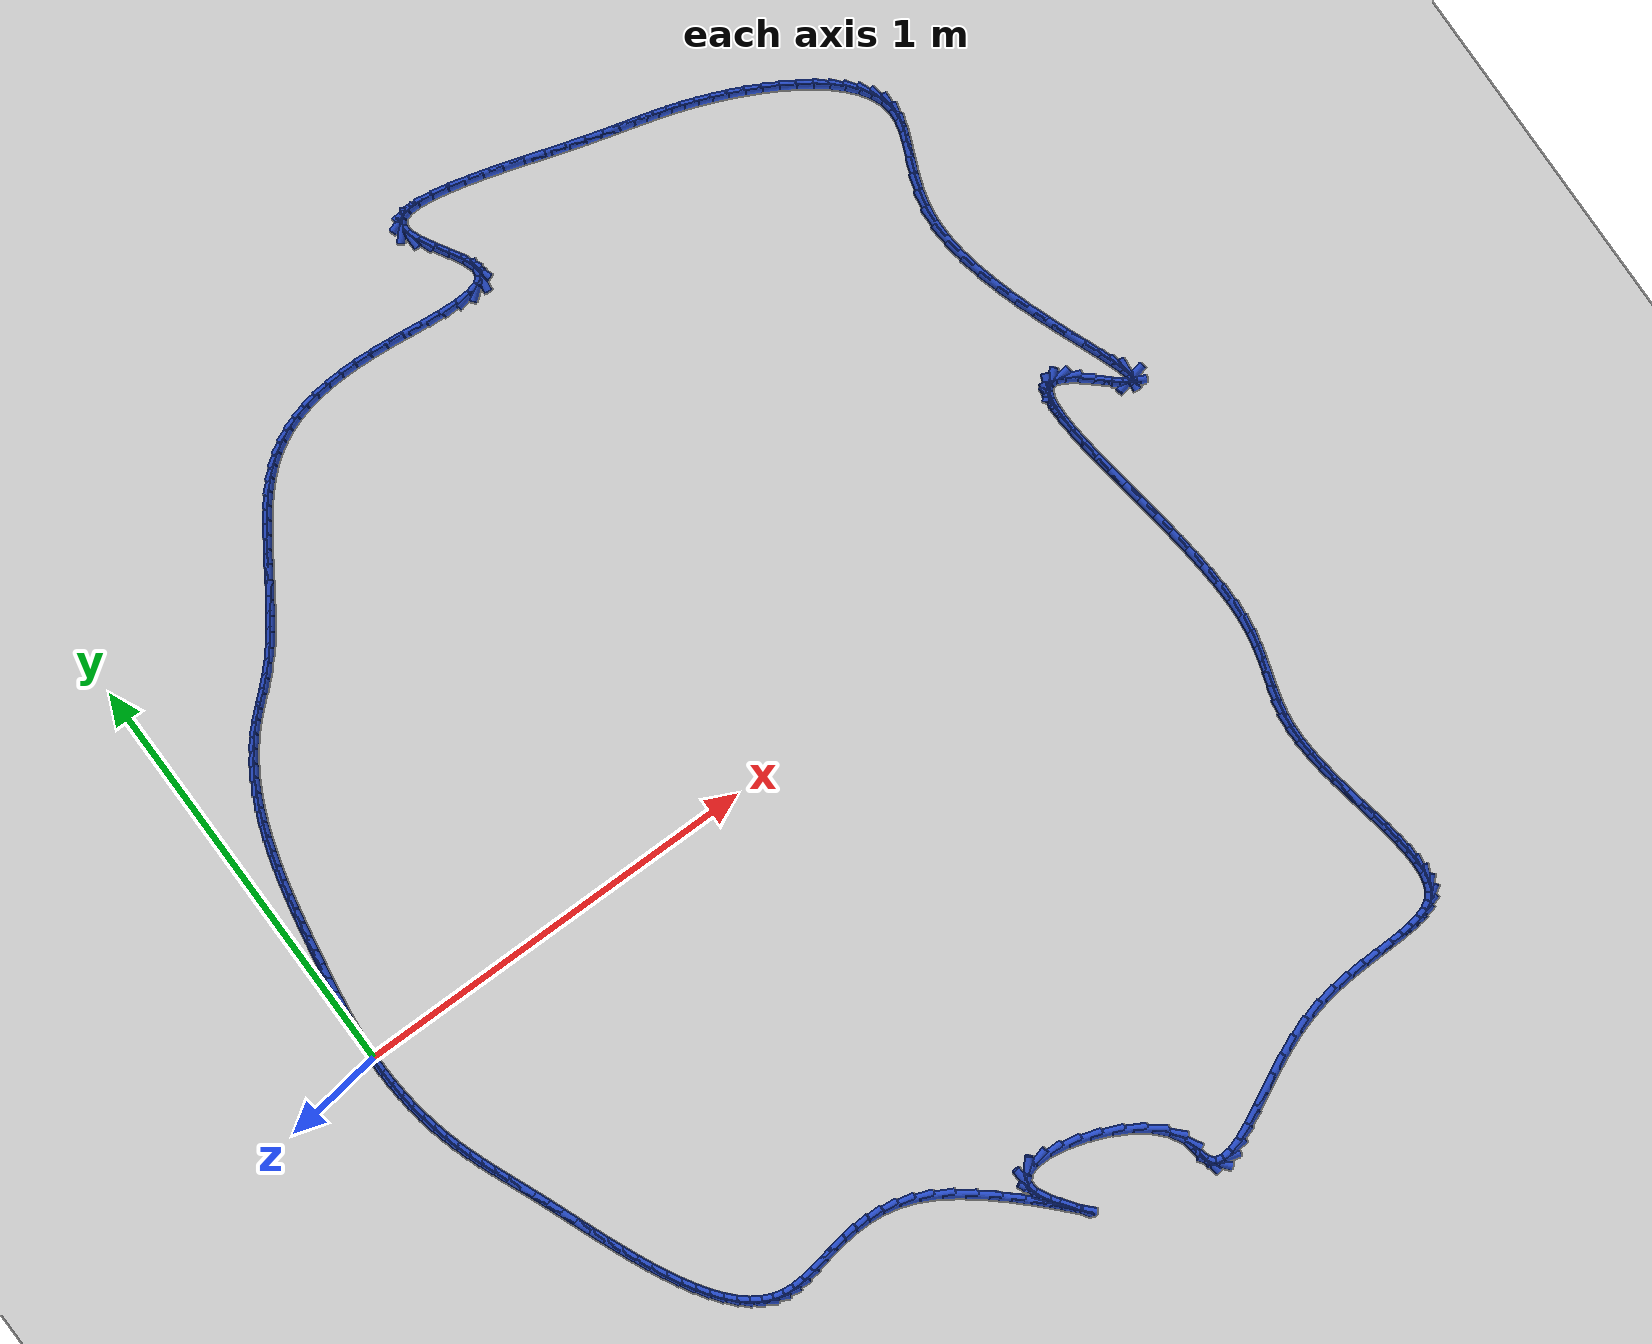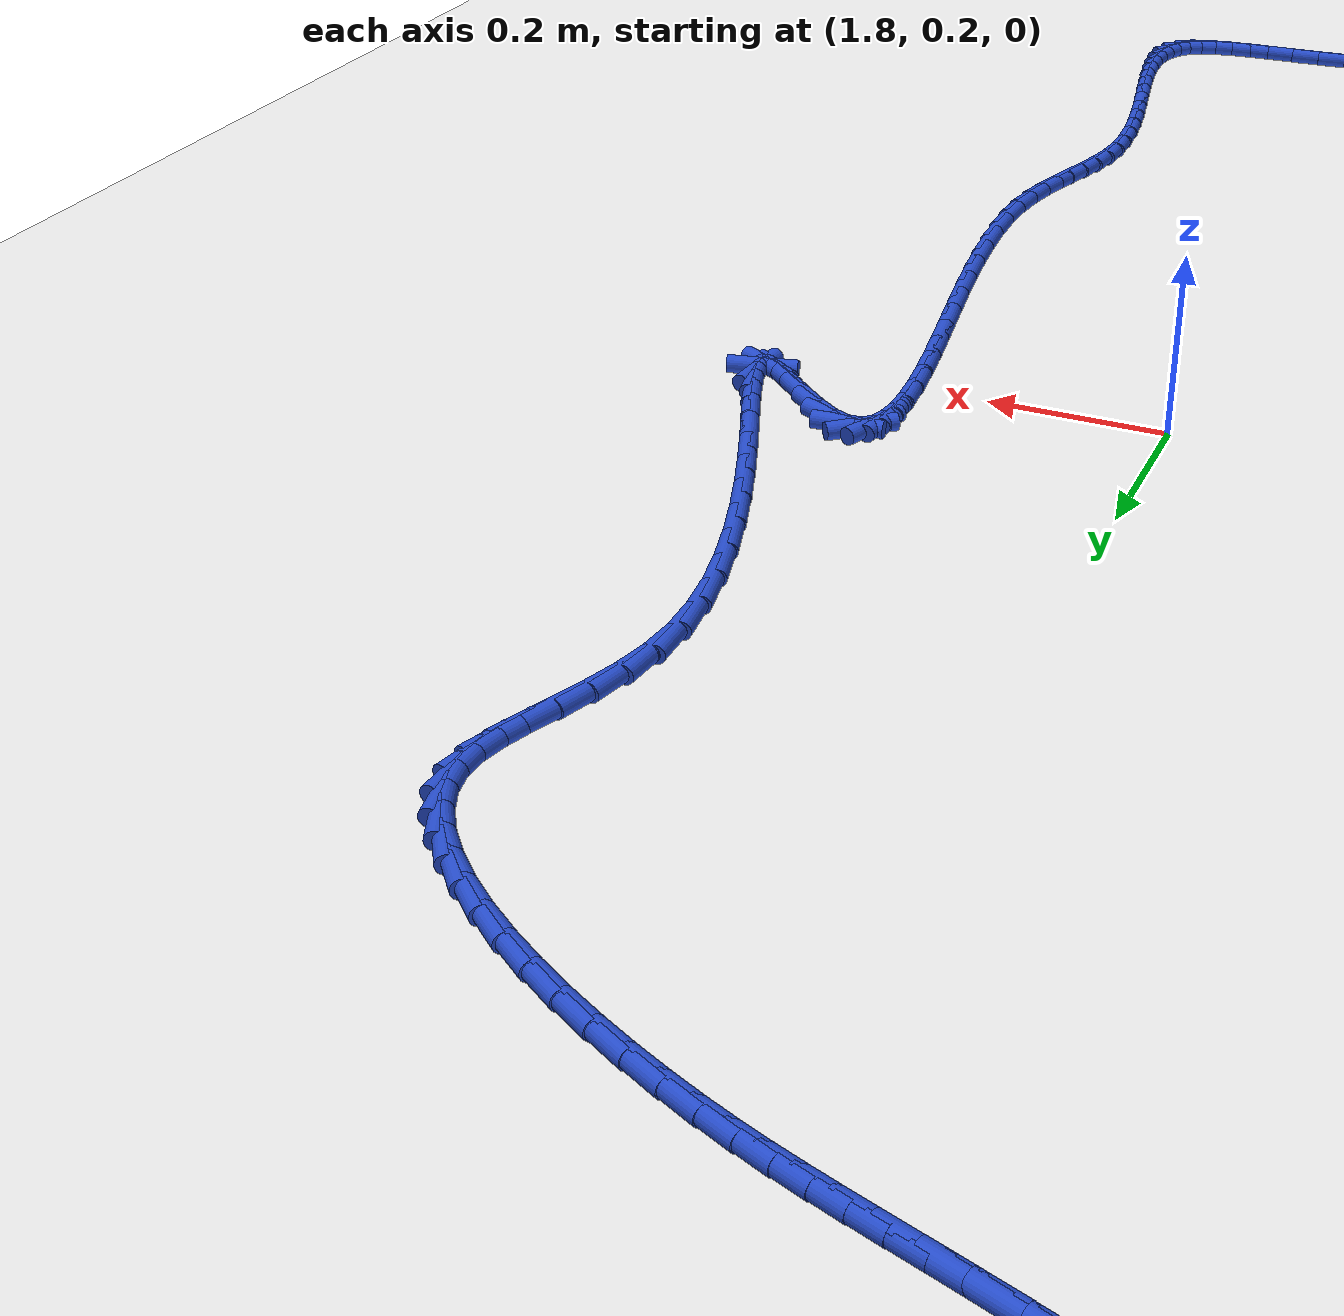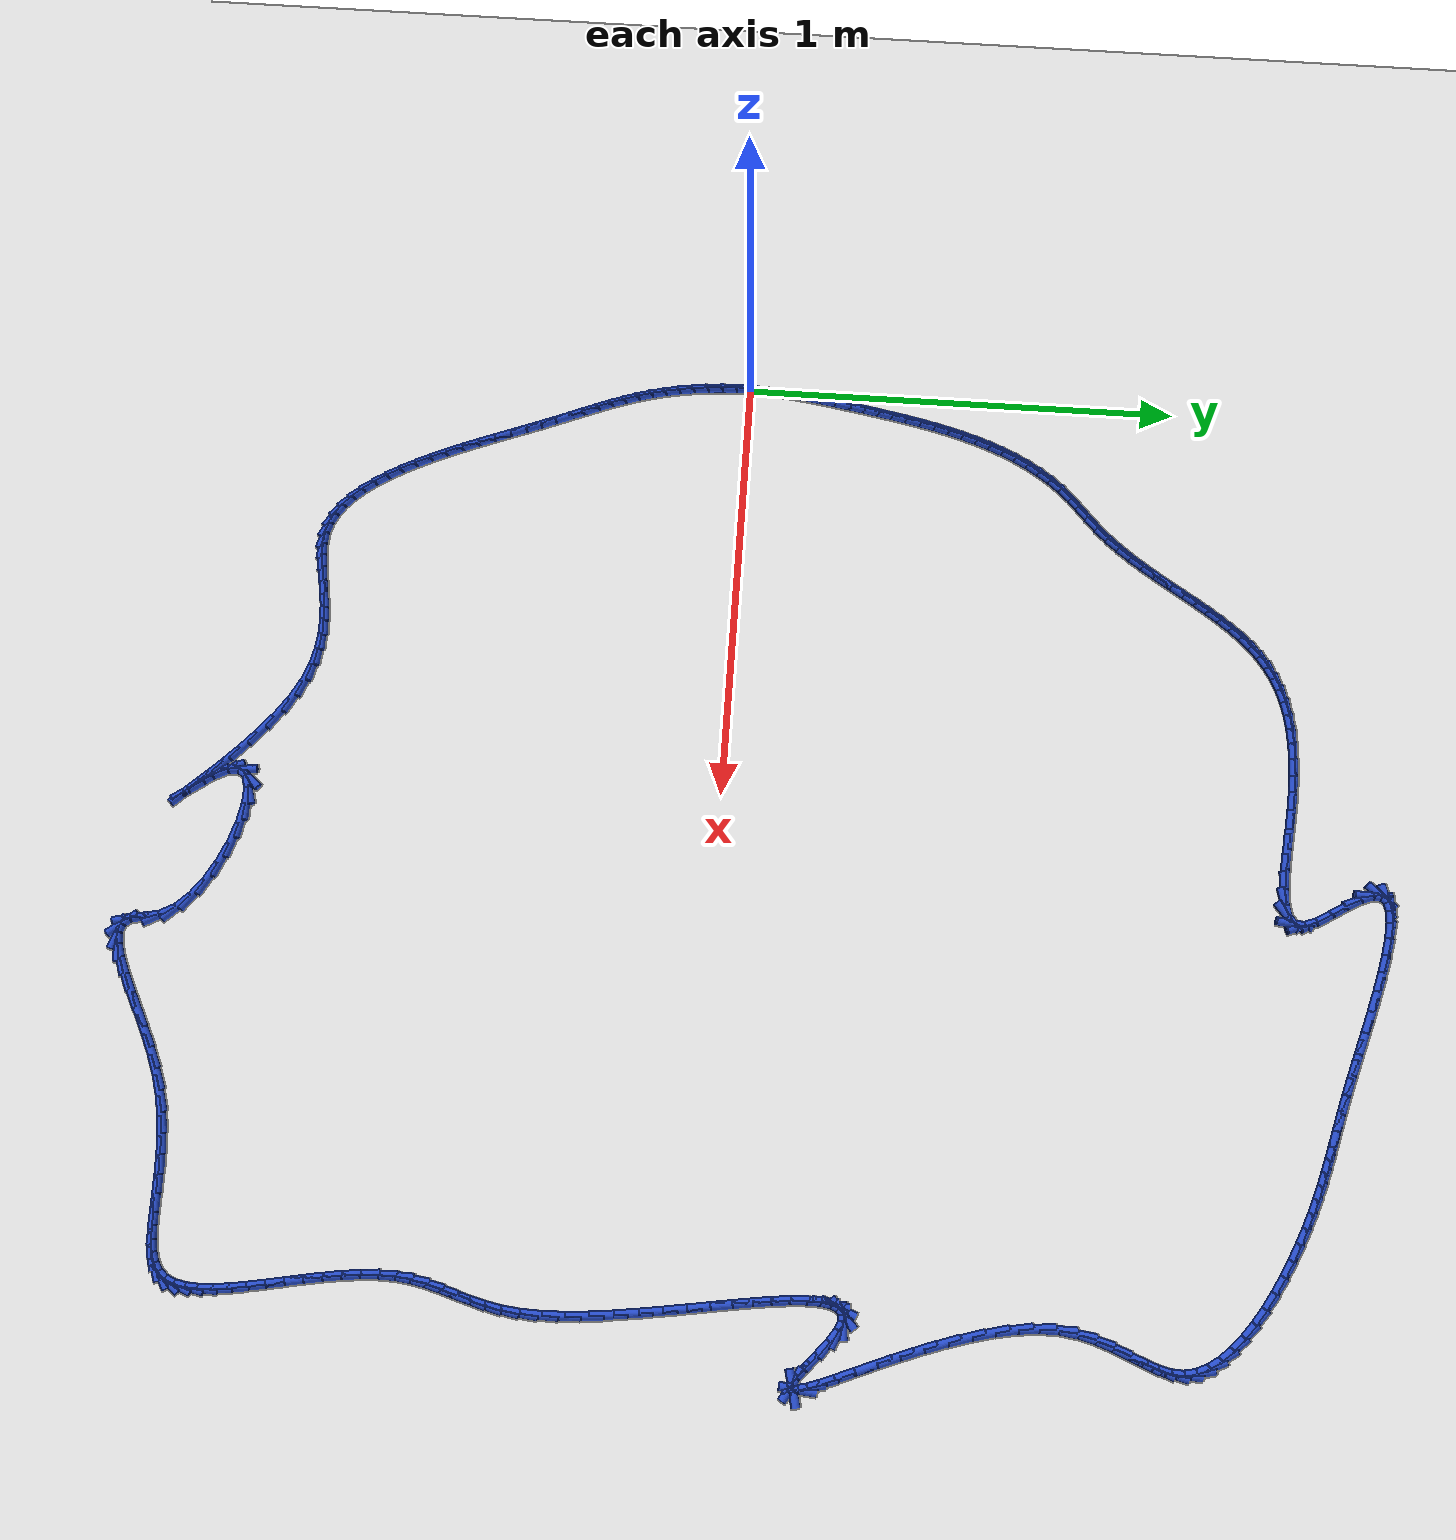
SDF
<sdf version="1.6">
 <world name="default">
  <light name="sun" type="directional">
   <pose>0 0 10 0 -0 0</pose>
   <diffuse>0.8 0.8 0.8 1</diffuse>
   <specular>0.2 0.2 0.2 1</specular>
   <attenuation>
    <range>1000</range>
    <constant>0.9</constant>
    <linear>0.01</linear>
    <quadratic>0.001</quadratic>
   </attenuation>
   <direction>-0.5 0.1 -0.9</direction>
  </light>
  <model name="ground_plane">
   <static>1</static>
   <link name="link">
    <collision name="collision">
     <geometry><plane><normal>0 0 1</normal><size>100 100</size></plane></geometry>
     <surface><friction><ode><mu>100</mu><mu2>50</mu2></ode></friction></surface>
    </collision>
    <visual name="visual">
     <cast_shadows>0</cast_shadows>
     <geometry><plane><normal>0 0 1</normal><size>100 100</size></plane></geometry>
     <material>
      <script><uri>file://media/materials/scripts/gazebo.material</uri><name>Gazebo/WhiteGlow</name></script>
     </material>
    </visual>
   </link>
  </model>
  <gravity>0 0 -9.8</gravity>
  <magnetic_field>6e-06 2.3e-05 -4.2e-05</magnetic_field>
  <atmosphere type="adiabatic"/>
  <physics name="default_physics" default="0" type="ode">
   <max_step_size>0.001</max_step_size>
   <real_time_factor>1</real_time_factor>
   <real_time_update_rate>1000</real_time_update_rate>
  </physics>
  <scene><ambient>0.4 0.4 0.4 1</ambient><background>0.7 0.7 0.7 1</background><shadows>1</shadows></scene>
  <spherical_coordinates>
   <surface_model>EARTH_WGS84</surface_model>
   <latitude_deg>0</latitude_deg>
   <longitude_deg>0</longitude_deg>
   <elevation>0</elevation>
   <heading_deg>0</heading_deg>
  </spherical_coordinates>
  <model name="line">
   <link name="link_0">
    <pose>8.673617379884035e-19 -3.469446951953614e-17 0.01 0 1.57 1.5308168019717938</pose>
    <collision name="collision">
     <geometry><cylinder><radius>0.01</radius><length>0.08</length></cylinder></geometry>
    </collision>
    <visual name="visual">
     <material>
      <script><name>Gazebo/Blue</name><uri>file://media/materials/scripts/gazebo.material</uri></script>
     </material>
     <geometry><cylinder><radius>0.01</radius><length>0.08</length></cylinder></geometry>
    </visual>
   </link>
   <link name="link_1">
    <pose>0.0013352738086139177 0.03338114501231601 0.01 0 1.57 1.495564774774981</pose>
    <collision name="collision">
     <geometry><cylinder><radius>0.01</radius><length>0.08</length></cylinder></geometry>
    </collision>
    <visual name="visual">
     <material>
      <script><name>Gazebo/Blue</name><uri>file://media/materials/scripts/gazebo.material</uri></script>
     </material>
     <geometry><cylinder><radius>0.01</radius><length>0.08</length></cylinder></geometry>
    </visual>
   </link>
   <link name="link_2">
    <pose>0.003835786866249393 0.0665559732999649 0.01 0 1.57 1.4654453502533111</pose>
    <collision name="collision">
     <geometry><cylinder><radius>0.01</radius><length>0.08</length></cylinder></geometry>
    </collision>
    <visual name="visual">
     <material>
      <script><name>Gazebo/Blue</name><uri>file://media/materials/scripts/gazebo.material</uri></script>
     </material>
     <geometry><cylinder><radius>0.01</radius><length>0.08</length></cylinder></geometry>
    </visual>
   </link>
   <link name="link_3">
    <pose>0.00733151701681408 0.09961487649468123 0.01 0 1.57 1.44072992684641</pose>
    <collision name="collision">
     <geometry><cylinder><radius>0.01</radius><length>0.08</length></cylinder></geometry>
    </collision>
    <visual name="visual">
     <material>
      <script><name>Gazebo/Blue</name><uri>file://media/materials/scripts/gazebo.material</uri></script>
     </material>
     <geometry><cylinder><radius>0.01</radius><length>0.08</length></cylinder></geometry>
    </visual>
   </link>
   <link name="link_4">
    <pose>0.011652442104215637 0.1326482462281996 0.01 0 1.57 1.421570619040127</pose>
    <collision name="collision">
     <geometry><cylinder><radius>0.01</radius><length>0.08</length></cylinder></geometry>
    </collision>
    <visual name="visual">
     <material>
      <script><name>Gazebo/Blue</name><uri>file://media/materials/scripts/gazebo.material</uri></script>
     </material>
     <geometry><cylinder><radius>0.01</radius><length>0.08</length></cylinder></geometry>
    </visual>
   </link>
   <link name="link_5">
    <pose>0.01662853997236172 0.16574647413225468 0.01 0 1.57 1.4080185188563408</pose>
    <collision name="collision">
     <geometry><cylinder><radius>0.01</radius><length>0.08</length></cylinder></geometry>
    </collision>
    <visual name="visual">
     <material>
      <script><name>Gazebo/Blue</name><uri>file://media/materials/scripts/gazebo.material</uri></script>
     </material>
     <geometry><cylinder><radius>0.01</radius><length>0.08</length></cylinder></geometry>
    </visual>
   </link>
   <link name="link_6">
    <pose>0.022089788465159993 0.19899995183858105 0.01 0 1.57 1.4000417860296894</pose>
    <collision name="collision">
     <geometry><cylinder><radius>0.01</radius><length>0.08</length></cylinder></geometry>
    </collision>
    <visual name="visual">
     <material>
      <script><name>Gazebo/Blue</name><uri>file://media/materials/scripts/gazebo.material</uri></script>
     </material>
     <geometry><cylinder><radius>0.01</radius><length>0.08</length></cylinder></geometry>
    </visual>
   </link>
   <link name="link_7">
    <pose>0.027866165426518093 0.2324990709789133 0.01 0 1.57 1.3967645328675942</pose>
    <collision name="collision">
     <geometry><cylinder><radius>0.01</radius><length>0.08</length></cylinder></geometry>
    </collision>
    <visual name="visual">
     <material>
      <script><name>Gazebo/Blue</name><uri>file://media/materials/scripts/gazebo.material</uri></script>
     </material>
     <geometry><cylinder><radius>0.01</radius><length>0.08</length></cylinder></geometry>
    </visual>
   </link>
   <link name="link_8">
    <pose>0.03381162684093896 0.26631654886136963 0.01 0 1.57 1.3923278908149244</pose>
    <collision name="collision">
     <geometry><cylinder><radius>0.01</radius><length>0.08</length></cylinder></geometry>
    </collision>
    <visual name="visual">
     <material>
      <script><name>Gazebo/Blue</name><uri>file://media/materials/scripts/gazebo.material</uri></script>
     </material>
     <geometry><cylinder><radius>0.01</radius><length>0.08</length></cylinder></geometry>
    </visual>
   </link>
   <link name="link_9">
    <pose>0.03995868702896481 0.300393487175124 0.01 0 1.57 1.3841546744231248</pose>
    <collision name="collision">
     <geometry><cylinder><radius>0.01</radius><length>0.08</length></cylinder></geometry>
    </collision>
    <visual name="visual">
     <material>
      <script><name>Gazebo/Blue</name><uri>file://media/materials/scripts/gazebo.material</uri></script>
     </material>
     <geometry><cylinder><radius>0.01</radius><length>0.08</length></cylinder></geometry>
    </visual>
   </link>
   <link name="link_10">
    <pose>0.04642041999198836 0.33461160694702885 0.01 0 1.57 1.3722293470910452</pose>
    <collision name="collision">
     <geometry><cylinder><radius>0.01</radius><length>0.08</length></cylinder></geometry>
    </collision>
    <visual name="visual">
     <material>
      <script><name>Gazebo/Blue</name><uri>file://media/materials/scripts/gazebo.material</uri></script>
     </material>
     <geometry><cylinder><radius>0.01</radius><length>0.08</length></cylinder></geometry>
    </visual>
   </link>
   <link name="link_11">
    <pose>0.05331029121193093 0.36885234064304756 0.01 0 1.57 1.3564924496723376</pose>
    <collision name="collision">
     <geometry><cylinder><radius>0.01</radius><length>0.08</length></cylinder></geometry>
    </collision>
    <visual name="visual">
     <material>
      <script><name>Gazebo/Blue</name><uri>file://media/materials/scripts/gazebo.material</uri></script>
     </material>
     <geometry><cylinder><radius>0.01</radius><length>0.08</length></cylinder></geometry>
    </visual>
   </link>
   <link name="link_12">
    <pose>0.060741766170713994 0.40299712072914445 0.01 0 1.57 1.336832508366309</pose>
    <collision name="collision">
     <geometry><cylinder><radius>0.01</radius><length>0.08</length></cylinder></geometry>
    </collision>
    <visual name="visual">
     <material>
      <script><name>Gazebo/Blue</name><uri>file://media/materials/scripts/gazebo.material</uri></script>
     </material>
     <geometry><cylinder><radius>0.01</radius><length>0.08</length></cylinder></geometry>
    </visual>
   </link>
   <link name="link_13">
    <pose>0.06882831035025888 0.4369273796712832 0.01 0 1.57 1.3130907788760848</pose>
    <collision name="collision">
     <geometry><cylinder><radius>0.01</radius><length>0.08</length></cylinder></geometry>
    </collision>
    <visual name="visual">
     <material>
      <script><name>Gazebo/Blue</name><uri>file://media/materials/scripts/gazebo.material</uri></script>
     </material>
     <geometry><cylinder><radius>0.01</radius><length>0.08</length></cylinder></geometry>
    </visual>
   </link>
   <link name="link_14">
    <pose>0.07768338923248697 0.4705245499354275 0.01 0 1.57 1.285067066201021</pose>
    <collision name="collision">
     <geometry><cylinder><radius>0.01</radius><length>0.08</length></cylinder></geometry>
    </collision>
    <visual name="visual">
     <material>
      <script><name>Gazebo/Blue</name><uri>file://media/materials/scripts/gazebo.material</uri></script>
     </material>
     <geometry><cylinder><radius>0.01</radius><length>0.08</length></cylinder></geometry>
    </visual>
   </link>
   <link name="link_15">
    <pose>0.08742046829931965 0.5036700639875412 0.01 0 1.57 1.2525277943087436</pose>
    <collision name="collision">
     <geometry><cylinder><radius>0.01</radius><length>0.08</length></cylinder></geometry>
    </collision>
    <visual name="visual">
     <material>
      <script><name>Gazebo/Blue</name><uri>file://media/materials/scripts/gazebo.material</uri></script>
     </material>
     <geometry><cylinder><radius>0.01</radius><length>0.08</length></cylinder></geometry>
    </visual>
   </link>
   <link name="link_16">
    <pose>0.09815301303267832 0.5362453542935881 0.01 0 1.57 1.2152177916173208</pose>
    <collision name="collision">
     <geometry><cylinder><radius>0.01</radius><length>0.08</length></cylinder></geometry>
    </collision>
    <visual name="visual">
     <material>
      <script><name>Gazebo/Blue</name><uri>file://media/materials/scripts/gazebo.material</uri></script>
     </material>
     <geometry><cylinder><radius>0.01</radius><length>0.08</length></cylinder></geometry>
    </visual>
   </link>
   <link name="link_17">
    <pose>0.10999448891448435 0.5681318533195325 0.01 0 1.57 1.1728775287144781</pose>
    <collision name="collision">
     <geometry><cylinder><radius>0.01</radius><length>0.08</length></cylinder></geometry>
    </collision>
    <visual name="visual">
     <material>
      <script><name>Gazebo/Blue</name><uri>file://media/materials/scripts/gazebo.material</uri></script>
     </material>
     <geometry><cylinder><radius>0.01</radius><length>0.08</length></cylinder></geometry>
    </visual>
   </link>
   <link name="link_18">
    <pose>0.12305836142665919 0.5992109935313377 0.01 0 1.57 1.1252676577298741</pose>
    <collision name="collision">
     <geometry><cylinder><radius>0.01</radius><length>0.08</length></cylinder></geometry>
    </collision>
    <visual name="visual">
     <material>
      <script><name>Gazebo/Blue</name><uri>file://media/materials/scripts/gazebo.material</uri></script>
     </material>
     <geometry><cylinder><radius>0.01</radius><length>0.08</length></cylinder></geometry>
    </visual>
   </link>
   <link name="link_19">
    <pose>0.13745809605112405 0.6293642073949672 0.01 0 1.57 1.0722024168929365</pose>
    <collision name="collision">
     <geometry><cylinder><radius>0.01</radius><length>0.08</length></cylinder></geometry>
    </collision>
    <visual name="visual">
     <material>
      <script><name>Gazebo/Blue</name><uri>file://media/materials/scripts/gazebo.material</uri></script>
     </material>
     <geometry><cylinder><radius>0.01</radius><length>0.08</length></cylinder></geometry>
    </visual>
   </link>
   <link name="link_20">
    <pose>0.15330715826980051 0.6584729273763859 0.01 0 1.57 1.013592426569128</pose>
    <collision name="collision">
     <geometry><cylinder><radius>0.01</radius><length>0.08</length></cylinder></geometry>
    </collision>
    <visual name="visual">
     <material>
      <script><name>Gazebo/Blue</name><uri>file://media/materials/scripts/gazebo.material</uri></script>
     </material>
     <geometry><cylinder><radius>0.01</radius><length>0.08</length></cylinder></geometry>
    </visual>
   </link>
   <link name="link_21">
    <pose>0.1707190135646099 0.6864185859415569 0.01 0 1.57 0.949495225820989</pose>
    <collision name="collision">
     <geometry><cylinder><radius>0.01</radius><length>0.08</length></cylinder></geometry>
    </collision>
    <visual name="visual">
     <material>
      <script><name>Gazebo/Blue</name><uri>file://media/materials/scripts/gazebo.material</uri></script>
     </material>
     <geometry><cylinder><radius>0.01</radius><length>0.08</length></cylinder></geometry>
    </visual>
   </link>
   <link name="link_22">
    <pose>0.1898071274174734 0.7130826155564437 0.01 0 1.57 0.8801683892164068</pose>
    <collision name="collision">
     <geometry><cylinder><radius>0.01</radius><length>0.08</length></cylinder></geometry>
    </collision>
    <visual name="visual">
     <material>
      <script><name>Gazebo/Blue</name><uri>file://media/materials/scripts/gazebo.material</uri></script>
     </material>
     <geometry><cylinder><radius>0.01</radius><length>0.08</length></cylinder></geometry>
    </visual>
   </link>
   <link name="link_23">
    <pose>0.21068496531031275 0.738346448687011 0.01 0 1.57 0.8062777518438228</pose>
    <collision name="collision">
     <geometry><cylinder><radius>0.01</radius><length>0.08</length></cylinder></geometry>
    </collision>
    <visual name="visual">
     <material>
      <script><name>Gazebo/Blue</name><uri>file://media/materials/scripts/gazebo.material</uri></script>
     </material>
     <geometry><cylinder><radius>0.01</radius><length>0.08</length></cylinder></geometry>
    </visual>
   </link>
   <link name="link_24">
    <pose>0.2334622415334083 0.7620953127659601 0.01 0 1.57 0.7441718822310409</pose>
    <collision name="collision">
     <geometry><cylinder><radius>0.01</radius><length>0.08</length></cylinder></geometry>
    </collision>
    <visual name="visual">
     <material>
      <script><name>Gazebo/Blue</name><uri>file://media/materials/scripts/gazebo.material</uri></script>
     </material>
     <geometry><cylinder><radius>0.01</radius><length>0.08</length></cylinder></geometry>
    </visual>
   </link>
   <link name="link_25">
    <pose>0.25788464767116 0.7845827059498105 0.01 0 1.57 0.7220642195083612</pose>
    <collision name="collision">
     <geometry><cylinder><radius>0.01</radius><length>0.08</length></cylinder></geometry>
    </collision>
    <visual name="visual">
     <material>
      <script><name>Gazebo/Blue</name><uri>file://media/materials/scripts/gazebo.material</uri></script>
     </material>
     <geometry><cylinder><radius>0.01</radius><length>0.08</length></cylinder></geometry>
    </visual>
   </link>
   <link name="link_26">
    <pose>0.283034707162935 0.8067330334809263 0.01 0 1.57 0.741799532435631</pose>
    <collision name="collision">
     <geometry><cylinder><radius>0.01</radius><length>0.08</length></cylinder></geometry>
    </collision>
    <visual name="visual">
     <material>
      <script><name>Gazebo/Blue</name><uri>file://media/materials/scripts/gazebo.material</uri></script>
     </material>
     <geometry><cylinder><radius>0.01</radius><length>0.08</length></cylinder></geometry>
    </visual>
   </link>
   <link name="link_27">
    <pose>0.3079245286135419 0.8295419371527748 0.01 0 1.57 0.7980756189737854</pose>
    <collision name="collision">
     <geometry><cylinder><radius>0.01</radius><length>0.08</length></cylinder></geometry>
    </collision>
    <visual name="visual">
     <material>
      <script><name>Gazebo/Blue</name><uri>file://media/materials/scripts/gazebo.material</uri></script>
     </material>
     <geometry><cylinder><radius>0.01</radius><length>0.08</length></cylinder></geometry>
    </visual>
   </link>
   <link name="link_28">
    <pose>0.3316665507922814 0.8538936988052274 0.01 0 1.57 0.857420101336595</pose>
    <collision name="collision">
     <geometry><cylinder><radius>0.01</radius><length>0.08</length></cylinder></geometry>
    </collision>
    <visual name="visual">
     <material>
      <script><name>Gazebo/Blue</name><uri>file://media/materials/scripts/gazebo.material</uri></script>
     </material>
     <geometry><cylinder><radius>0.01</radius><length>0.08</length></cylinder></geometry>
    </visual>
   </link>
   <link name="link_29">
    <pose>0.35412210044219655 0.87984138336121 0.01 0 1.57 0.9052558455693228</pose>
    <collision name="collision">
     <geometry><cylinder><radius>0.01</radius><length>0.08</length></cylinder></geometry>
    </collision>
    <visual name="visual">
     <material>
      <script><name>Gazebo/Blue</name><uri>file://media/materials/scripts/gazebo.material</uri></script>
     </material>
     <geometry><cylinder><radius>0.01</radius><length>0.08</length></cylinder></geometry>
    </visual>
   </link>
   <link name="link_30">
    <pose>0.37549106996375975 0.9070622698960747 0.01 0 1.57 0.9420693465753704</pose>
    <collision name="collision">
     <geometry><cylinder><radius>0.01</radius><length>0.08</length></cylinder></geometry>
    </collision>
    <visual name="visual">
     <material>
      <script><name>Gazebo/Blue</name><uri>file://media/materials/scripts/gazebo.material</uri></script>
     </material>
     <geometry><cylinder><radius>0.01</radius><length>0.08</length></cylinder></geometry>
    </visual>
   </link>
   <link name="link_31">
    <pose>0.3959750121691745 0.9352317945362039 0.01 0 1.57 0.9683941754711244</pose>
    <collision name="collision">
     <geometry><cylinder><radius>0.01</radius><length>0.08</length></cylinder></geometry>
    </collision>
    <visual name="visual">
     <material>
      <script><name>Gazebo/Blue</name><uri>file://media/materials/scripts/gazebo.material</uri></script>
     </material>
     <geometry><cylinder><radius>0.01</radius><length>0.08</length></cylinder></geometry>
    </visual>
   </link>
   <link name="link_32">
    <pose>0.41577547987064406 0.9640253934079792 0.01 0 1.57 0.9846249393287476</pose>
    <collision name="collision">
     <geometry><cylinder><radius>0.01</radius><length>0.08</length></cylinder></geometry>
    </collision>
    <visual name="visual">
     <material>
      <script><name>Gazebo/Blue</name><uri>file://media/materials/scripts/gazebo.material</uri></script>
     </material>
     <geometry><cylinder><radius>0.01</radius><length>0.08</length></cylinder></geometry>
    </visual>
   </link>
   <link name="link_33">
    <pose>0.4350940258803716 0.9931185026377829 0.01 0 1.57 0.9909478830847113</pose>
    <collision name="collision">
     <geometry><cylinder><radius>0.01</radius><length>0.08</length></cylinder></geometry>
    </collision>
    <visual name="visual">
     <material>
      <script><name>Gazebo/Blue</name><uri>file://media/materials/scripts/gazebo.material</uri></script>
     </material>
     <geometry><cylinder><radius>0.01</radius><length>0.08</length></cylinder></geometry>
    </visual>
   </link>
   <link name="link_34">
    <pose>0.45413220301056095 1.022186558351997 0.01 0 1.57 0.9872974026348569</pose>
    <collision name="collision">
     <geometry><cylinder><radius>0.01</radius><length>0.08</length></cylinder></geometry>
    </collision>
    <visual name="visual">
     <material>
      <script><name>Gazebo/Blue</name><uri>file://media/materials/scripts/gazebo.material</uri></script>
     </material>
     <geometry><cylinder><radius>0.01</radius><length>0.08</length></cylinder></geometry>
    </visual>
   </link>
   <link name="link_35">
    <pose>0.4730915640734149 1.0509049966770025 0.01 0 1.57 0.9733270558147714</pose>
    <collision name="collision">
     <geometry><cylinder><radius>0.01</radius><length>0.08</length></cylinder></geometry>
    </collision>
    <visual name="visual">
     <material>
      <script><name>Gazebo/Blue</name><uri>file://media/materials/scripts/gazebo.material</uri></script>
     </material>
     <geometry><cylinder><radius>0.01</radius><length>0.08</length></cylinder></geometry>
    </visual>
   </link>
   <link name="link_36">
    <pose>0.49217366188113687 1.0789492537391823 0.01 0 1.57 0.9483916117289946</pose>
    <collision name="collision">
     <geometry><cylinder><radius>0.01</radius><length>0.08</length></cylinder></geometry>
    </collision>
    <visual name="visual">
     <material>
      <script><name>Gazebo/Blue</name><uri>file://media/materials/scripts/gazebo.material</uri></script>
     </material>
     <geometry><cylinder><radius>0.01</radius><length>0.08</length></cylinder></geometry>
    </visual>
   </link>
   <link name="link_37">
    <pose>0.5115800492459304 1.1059947656649183 0.01 0 1.57 0.9115464368631934</pose>
    <collision name="collision">
     <geometry><cylinder><radius>0.01</radius><length>0.08</length></cylinder></geometry>
    </collision>
    <visual name="visual">
     <material>
      <script><name>Gazebo/Blue</name><uri>file://media/materials/scripts/gazebo.material</uri></script>
     </material>
     <geometry><cylinder><radius>0.01</radius><length>0.08</length></cylinder></geometry>
    </visual>
   </link>
   <link name="link_38">
    <pose>0.5315122789799988 1.1317169685805926 0.01 0 1.57 0.8615840476436292</pose>
    <collision name="collision">
     <geometry><cylinder><radius>0.01</radius><length>0.08</length></cylinder></geometry>
    </collision>
    <visual name="visual">
     <material>
      <script><name>Gazebo/Blue</name><uri>file://media/materials/scripts/gazebo.material</uri></script>
     </material>
     <geometry><cylinder><radius>0.01</radius><length>0.08</length></cylinder></geometry>
    </visual>
   </link>
   <link name="link_39">
    <pose>0.5521719038955452 1.1557912986125864 0.01 0 1.57 0.7971466475119076</pose>
    <collision name="collision">
     <geometry><cylinder><radius>0.01</radius><length>0.08</length></cylinder></geometry>
    </collision>
    <visual name="visual">
     <material>
      <script><name>Gazebo/Blue</name><uri>file://media/materials/scripts/gazebo.material</uri></script>
     </material>
     <geometry><cylinder><radius>0.01</radius><length>0.08</length></cylinder></geometry>
    </visual>
   </link>
   <link name="link_40">
    <pose>0.5737604768047733 1.177893191887283 0.01 0 1.57 0.7169901733976811</pose>
    <collision name="collision">
     <geometry><cylinder><radius>0.01</radius><length>0.08</length></cylinder></geometry>
    </collision>
    <visual name="visual">
     <material>
      <script><name>Gazebo/Blue</name><uri>file://media/materials/scripts/gazebo.material</uri></script>
     </material>
     <geometry><cylinder><radius>0.01</radius><length>0.08</length></cylinder></geometry>
    </visual>
   </link>
   <link name="link_41">
    <pose>0.596479441783193 1.1976986035114925 0.01 0 1.57 0.6240112115377533</pose>
    <collision name="collision">
     <geometry><cylinder><radius>0.01</radius><length>0.08</length></cylinder></geometry>
    </collision>
    <visual name="visual">
     <material>
      <script><name>Gazebo/Blue</name><uri>file://media/materials/scripts/gazebo.material</uri></script>
     </material>
     <geometry><cylinder><radius>0.01</radius><length>0.08</length></cylinder></geometry>
    </visual>
   </link>
   <link name="link_42">
    <pose>0.6205063462961077 1.2149975427597464 0.01 0 1.57 0.5277248260851769</pose>
    <collision name="collision">
     <geometry><cylinder><radius>0.01</radius><length>0.08</length></cylinder></geometry>
    </collision>
    <visual name="visual">
     <material>
      <script><name>Gazebo/Blue</name><uri>file://media/materials/scripts/gazebo.material</uri></script>
     </material>
     <geometry><cylinder><radius>0.01</radius><length>0.08</length></cylinder></geometry>
    </visual>
   </link>
   <link name="link_43">
    <pose>0.6459650005336381 1.229836497132707 0.01 0 1.57 0.43227836846111106</pose>
    <collision name="collision">
     <geometry><cylinder><radius>0.01</radius><length>0.08</length></cylinder></geometry>
    </collision>
    <visual name="visual">
     <material>
      <script><name>Gazebo/Blue</name><uri>file://media/materials/scripts/gazebo.material</uri></script>
     </material>
     <geometry><cylinder><radius>0.01</radius><length>0.08</length></cylinder></geometry>
    </visual>
   </link>
   <link name="link_44">
    <pose>0.6729718780167485 1.2422969707165374 0.01 0 1.57 0.34066023680113444</pose>
    <collision name="collision">
     <geometry><cylinder><radius>0.01</radius><length>0.08</length></cylinder></geometry>
    </collision>
    <visual name="visual">
     <material>
      <script><name>Gazebo/Blue</name><uri>file://media/materials/scripts/gazebo.material</uri></script>
     </material>
     <geometry><cylinder><radius>0.01</radius><length>0.08</length></cylinder></geometry>
    </visual>
   </link>
   <link name="link_45">
    <pose>0.7016434522664027 1.2524604675974003 0.01 0 1.57 0.25530014319455663</pose>
    <collision name="collision">
     <geometry><cylinder><radius>0.01</radius><length>0.08</length></cylinder></geometry>
    </collision>
    <visual name="visual">
     <material>
      <script><name>Gazebo/Blue</name><uri>file://media/materials/scripts/gazebo.material</uri></script>
     </material>
     <geometry><cylinder><radius>0.01</radius><length>0.08</length></cylinder></geometry>
    </visual>
   </link>
   <link name="link_46">
    <pose>0.7320961968035657 1.2604084918614584 0.01 0 1.57 0.1778230280413665</pose>
    <collision name="collision">
     <geometry><cylinder><radius>0.01</radius><length>0.08</length></cylinder></geometry>
    </collision>
    <visual name="visual">
     <material>
      <script><name>Gazebo/Blue</name><uri>file://media/materials/scripts/gazebo.material</uri></script>
     </material>
     <geometry><cylinder><radius>0.01</radius><length>0.08</length></cylinder></geometry>
    </visual>
   </link>
   <link name="link_47">
    <pose>0.7644465851492007 1.2662225475948747 0.01 0 1.57 0.10902746097904381</pose>
    <collision name="collision">
     <geometry><cylinder><radius>0.01</radius><length>0.08</length></cylinder></geometry>
    </collision>
    <visual name="visual">
     <material>
      <script><name>Gazebo/Blue</name><uri>file://media/materials/scripts/gazebo.material</uri></script>
     </material>
     <geometry><cylinder><radius>0.01</radius><length>0.08</length></cylinder></geometry>
    </visual>
   </link>
   <link name="link_48">
    <pose>0.7988110908242723 1.2699841388838116 0.01 0 1.57 0.04902565736827293</pose>
    <collision name="collision">
     <geometry><cylinder><radius>0.01</radius><length>0.08</length></cylinder></geometry>
    </collision>
    <visual name="visual">
     <material>
      <script><name>Gazebo/Blue</name><uri>file://media/materials/scripts/gazebo.material</uri></script>
     </material>
     <geometry><cylinder><radius>0.01</radius><length>0.08</length></cylinder></geometry>
    </visual>
   </link>
   <link name="link_49">
    <pose>0.8353061873497442 1.2717747698144317 0.01 0 1.57 -0.0025508418967830513</pose>
    <collision name="collision">
     <geometry><cylinder><radius>0.01</radius><length>0.08</length></cylinder></geometry>
    </collision>
    <visual name="visual">
     <material>
      <script><name>Gazebo/Blue</name><uri>file://media/materials/scripts/gazebo.material</uri></script>
     </material>
     <geometry><cylinder><radius>0.01</radius><length>0.08</length></cylinder></geometry>
    </visual>
   </link>
   <link name="link_50">
    <pose>0.8740483482465817 1.2716759444728987 0.01 0 1.57 -0.04635395328040502</pose>
    <collision name="collision">
     <geometry><cylinder><radius>0.01</radius><length>0.08</length></cylinder></geometry>
    </collision>
    <visual name="visual">
     <material>
      <script><name>Gazebo/Blue</name><uri>file://media/materials/scripts/gazebo.material</uri></script>
     </material>
     <geometry><cylinder><radius>0.01</radius><length>0.08</length></cylinder></geometry>
    </visual>
   </link>
   <link name="link_51">
    <pose>0.9151540470357482 1.2697691669453743 0.01 0 1.57 -0.08316591058556339</pose>
    <collision name="collision">
     <geometry><cylinder><radius>0.01</radius><length>0.08</length></cylinder></geometry>
    </collision>
    <visual name="visual">
     <material>
      <script><name>Gazebo/Blue</name><uri>file://media/materials/scripts/gazebo.material</uri></script>
     </material>
     <geometry><cylinder><radius>0.01</radius><length>0.08</length></cylinder></geometry>
    </visual>
   </link>
   <link name="link_52">
    <pose>0.9587397572382077 1.266135941318022 0.01 0 1.57 -0.11112628012779982</pose>
    <collision name="collision">
     <geometry><cylinder><radius>0.01</radius><length>0.08</length></cylinder></geometry>
    </collision>
    <visual name="visual">
     <material>
      <script><name>Gazebo/Blue</name><uri>file://media/materials/scripts/gazebo.material</uri></script>
     </material>
     <geometry><cylinder><radius>0.01</radius><length>0.08</length></cylinder></geometry>
    </visual>
   </link>
   <link name="link_53">
    <pose>1.0046283662649889 1.2610154156473448 0.01 0 1.57 -0.11852309784575374</pose>
    <collision name="collision">
     <geometry><cylinder><radius>0.01</radius><length>0.08</length></cylinder></geometry>
    </collision>
    <visual name="visual">
     <material>
      <script><name>Gazebo/Blue</name><uri>file://media/materials/scripts/gazebo.material</uri></script>
     </material>
     <geometry><cylinder><radius>0.01</radius><length>0.08</length></cylinder></geometry>
    </visual>
   </link>
   <link name="link_54">
    <pose>1.051084738678082 1.255483333794247 0.01 0 1.57 -0.10218950490863456</pose>
    <collision name="collision">
     <geometry><cylinder><radius>0.01</radius><length>0.08</length></cylinder></geometry>
    </collision>
    <visual name="visual">
     <material>
      <script><name>Gazebo/Blue</name><uri>file://media/materials/scripts/gazebo.material</uri></script>
     </material>
     <geometry><cylinder><radius>0.01</radius><length>0.08</length></cylinder></geometry>
    </visual>
   </link>
   <link name="link_55">
    <pose>1.095858892195806 1.250891891733022 0.01 0 1.57 -0.05621739479275595</pose>
    <collision name="collision">
     <geometry><cylinder><radius>0.01</radius><length>0.08</length></cylinder></geometry>
    </collision>
    <visual name="visual">
     <material>
      <script><name>Gazebo/Blue</name><uri>file://media/materials/scripts/gazebo.material</uri></script>
     </material>
     <geometry><cylinder><radius>0.01</radius><length>0.08</length></cylinder></geometry>
    </visual>
   </link>
   <link name="link_56">
    <pose>1.1367005193973914 1.2485934600246182 0.01 0 1.57 0.038843582428906565</pose>
    <collision name="collision">
     <geometry><cylinder><radius>0.01</radius><length>0.08</length></cylinder></geometry>
    </collision>
    <visual name="visual">
     <material>
      <script><name>Gazebo/Blue</name><uri>file://media/materials/scripts/gazebo.material</uri></script>
     </material>
     <geometry><cylinder><radius>0.01</radius><length>0.08</length></cylinder></geometry>
    </visual>
   </link>
   <link name="link_57">
    <pose>1.1713593128620694 1.2499404092299844 0.01 0 1.57 0.23736649497310514</pose>
    <collision name="collision">
     <geometry><cylinder><radius>0.01</radius><length>0.08</length></cylinder></geometry>
    </collision>
    <visual name="visual">
     <material>
      <script><name>Gazebo/Blue</name><uri>file://media/materials/scripts/gazebo.material</uri></script>
     </material>
     <geometry><cylinder><radius>0.01</radius><length>0.08</length></cylinder></geometry>
    </visual>
   </link>
   <link name="link_58">
    <pose>1.1975849651690709 1.2562851099100683 0.01 0 1.57 0.6848993251407175</pose>
    <collision name="collision">
     <geometry><cylinder><radius>0.01</radius><length>0.08</length></cylinder></geometry>
    </collision>
    <visual name="visual">
     <material>
      <script><name>Gazebo/Blue</name><uri>file://media/materials/scripts/gazebo.material</uri></script>
     </material>
     <geometry><cylinder><radius>0.01</radius><length>0.08</length></cylinder></geometry>
    </visual>
   </link>
   <link name="link_59">
    <pose>1.2131271688976257 1.2689799326258182 0.01 0 1.57 1.441574710932317</pose>
    <collision name="collision">
     <geometry><cylinder><radius>0.01</radius><length>0.08</length></cylinder></geometry>
    </collision>
    <visual name="visual">
     <material>
      <script><name>Gazebo/Blue</name><uri>file://media/materials/scripts/gazebo.material</uri></script>
     </material>
     <geometry><cylinder><radius>0.01</radius><length>0.08</length></cylinder></geometry>
    </visual>
   </link>
   <link name="link_60">
    <pose>1.2157745795685786 1.2893531382696346 0.01 0 1.57 -1.2304302910337432</pose>
    <collision name="collision">
     <geometry><cylinder><radius>0.01</radius><length>0.08</length></cylinder></geometry>
    </collision>
    <visual name="visual">
     <material>
      <script><name>Gazebo/Blue</name><uri>file://media/materials/scripts/gazebo.material</uri></script>
     </material>
     <geometry><cylinder><radius>0.01</radius><length>0.08</length></cylinder></geometry>
    </visual>
   </link>
   <link name="link_61">
    <pose>1.2059461501882858 1.3171054001357274 0.01 0 1.57 -1.0698379763237298</pose>
    <collision name="collision">
     <geometry><cylinder><radius>0.01</radius><length>0.08</length></cylinder></geometry>
    </collision>
    <visual name="visual">
     <material>
      <script><name>Gazebo/Blue</name><uri>file://media/materials/scripts/gazebo.material</uri></script>
     </material>
     <geometry><cylinder><radius>0.01</radius><length>0.08</length></cylinder></geometry>
    </visual>
   </link>
   <link name="link_62">
    <pose>1.188315530916816 1.3493046504083843 0.01 0 1.57 -1.0240971223593052</pose>
    <collision name="collision">
     <geometry><cylinder><radius>0.01</radius><length>0.08</length></cylinder></geometry>
    </collision>
    <visual name="visual">
     <material>
      <script><name>Gazebo/Blue</name><uri>file://media/materials/scripts/gazebo.material</uri></script>
     </material>
     <geometry><cylinder><radius>0.01</radius><length>0.08</length></cylinder></geometry>
    </visual>
   </link>
   <link name="link_63">
    <pose>1.1679439589579075 1.3827789883750543 0.01 0 1.57 -1.0514834174310226</pose>
    <collision name="collision">
     <geometry><cylinder><radius>0.01</radius><length>0.08</length></cylinder></geometry>
    </collision>
    <visual name="visual">
     <material>
      <script><name>Gazebo/Blue</name><uri>file://media/materials/scripts/gazebo.material</uri></script>
     </material>
     <geometry><cylinder><radius>0.01</radius><length>0.08</length></cylinder></geometry>
    </visual>
   </link>
   <link name="link_64">
    <pose>1.149892671515298 1.4143565133231863 0.01 0 1.57 -1.1880713635314355</pose>
    <collision name="collision">
     <geometry><cylinder><radius>0.01</radius><length>0.08</length></cylinder></geometry>
    </collision>
    <visual name="visual">
     <material>
      <script><name>Gazebo/Blue</name><uri>file://media/materials/scripts/gazebo.material</uri></script>
     </material>
     <geometry><cylinder><radius>0.01</radius><length>0.08</length></cylinder></geometry>
    </visual>
   </link>
   <link name="link_65">
    <pose>1.139220179012301 1.4408670268113075 0.01 0 1.57 1.5591934741708928</pose>
    <collision name="collision">
     <geometry><cylinder><radius>0.01</radius><length>0.08</length></cylinder></geometry>
    </collision>
    <visual name="visual">
     <material>
      <script><name>Gazebo/Blue</name><uri>file://media/materials/scripts/gazebo.material</uri></script>
     </material>
     <geometry><cylinder><radius>0.01</radius><length>0.08</length></cylinder></geometry>
    </visual>
   </link>
   <link name="link_66">
    <pose>1.1394433780248574 1.4601027271649014 0.01 0 1.57 0.8638376838934936</pose>
    <collision name="collision">
     <geometry><cylinder><radius>0.01</radius><length>0.08</length></cylinder></geometry>
    </collision>
    <visual name="visual">
     <material>
      <script><name>Gazebo/Blue</name><uri>file://media/materials/scripts/gazebo.material</uri></script>
     </material>
     <geometry><cylinder><radius>0.01</radius><length>0.08</length></cylinder></geometry>
    </visual>
   </link>
   <link name="link_67">
    <pose>1.1499676388981648 1.4724225511689326 0.01 0 1.57 0.306419315666187</pose>
    <collision name="collision">
     <geometry><cylinder><radius>0.01</radius><length>0.08</length></cylinder></geometry>
    </collision>
    <visual name="visual">
     <material>
      <script><name>Gazebo/Blue</name><uri>file://media/materials/scripts/gazebo.material</uri></script>
     </material>
     <geometry><cylinder><radius>0.01</radius><length>0.08</length></cylinder></geometry>
    </visual>
   </link>
   <link name="link_68">
    <pose>1.169520319075322 1.4786087046559573 0.01 0 1.57 0.030555699995595285</pose>
    <collision name="collision">
     <geometry><cylinder><radius>0.01</radius><length>0.08</length></cylinder></geometry>
    </collision>
    <visual name="visual">
     <material>
      <script><name>Gazebo/Blue</name><uri>file://media/materials/scripts/gazebo.material</uri></script>
     </material>
     <geometry><cylinder><radius>0.01</radius><length>0.08</length></cylinder></geometry>
    </visual>
   </link>
   <link name="link_69">
    <pose>1.1968287759994303 1.4794433934585334 0.01 0 1.57 -0.11007104141596746</pose>
    <collision name="collision">
     <geometry><cylinder><radius>0.01</radius><length>0.08</length></cylinder></geometry>
    </collision>
    <visual name="visual">
     <material>
      <script><name>Gazebo/Blue</name><uri>file://media/materials/scripts/gazebo.material</uri></script>
     </material>
     <geometry><cylinder><radius>0.01</radius><length>0.08</length></cylinder></geometry>
    </visual>
   </link>
   <link name="link_70">
    <pose>1.2306203671135896 1.475708823409219 0.01 0 1.57 -0.19051296776615328</pose>
    <collision name="collision">
     <geometry><cylinder><radius>0.01</radius><length>0.08</length></cylinder></geometry>
    </collision>
    <visual name="visual">
     <material>
      <script><name>Gazebo/Blue</name><uri>file://media/materials/scripts/gazebo.material</uri></script>
     </material>
     <geometry><cylinder><radius>0.01</radius><length>0.08</length></cylinder></geometry>
    </visual>
   </link>
   <link name="link_71">
    <pose>1.2696224498608981 1.4681872003405705 0.01 0 1.57 -0.24040319338311478</pose>
    <collision name="collision">
     <geometry><cylinder><radius>0.01</radius><length>0.08</length></cylinder></geometry>
    </collision>
    <visual name="visual">
     <material>
      <script><name>Gazebo/Blue</name><uri>file://media/materials/scripts/gazebo.material</uri></script>
     </material>
     <geometry><cylinder><radius>0.01</radius><length>0.08</length></cylinder></geometry>
    </visual>
   </link>
   <link name="link_72">
    <pose>1.3125623816844578 1.4576607300851463 0.01 0 1.57 -0.2725953391649666</pose>
    <collision name="collision">
     <geometry><cylinder><radius>0.01</radius><length>0.08</length></cylinder></geometry>
    </collision>
    <visual name="visual">
     <material>
      <script><name>Gazebo/Blue</name><uri>file://media/materials/scripts/gazebo.material</uri></script>
     </material>
     <geometry><cylinder><radius>0.01</radius><length>0.08</length></cylinder></geometry>
    </visual>
   </link>
   <link name="link_73">
    <pose>1.3581675200273675 1.444911618475503 0.01 0 1.57 -0.2932173468096086</pose>
    <collision name="collision">
     <geometry><cylinder><radius>0.01</radius><length>0.08</length></cylinder></geometry>
    </collision>
    <visual name="visual">
     <material>
      <script><name>Gazebo/Blue</name><uri>file://media/materials/scripts/gazebo.material</uri></script>
     </material>
     <geometry><cylinder><radius>0.01</radius><length>0.08</length></cylinder></geometry>
    </visual>
   </link>
   <link name="link_74">
    <pose>1.405165222332727 1.430722071344198 0.01 0 1.57 -0.3052713640028765</pose>
    <collision name="collision">
     <geometry><cylinder><radius>0.01</radius><length>0.08</length></cylinder></geometry>
    </collision>
    <visual name="visual">
     <material>
      <script><name>Gazebo/Blue</name><uri>file://media/materials/scripts/gazebo.material</uri></script>
     </material>
     <geometry><cylinder><radius>0.01</radius><length>0.08</length></cylinder></geometry>
    </visual>
   </link>
   <link name="link_75">
    <pose>1.452282846043637 1.4158742945237885 0.01 0 1.57 -0.3099995682612716</pose>
    <collision name="collision">
     <geometry><cylinder><radius>0.01</radius><length>0.08</length></cylinder></geometry>
    </collision>
    <visual name="visual">
     <material>
      <script><name>Gazebo/Blue</name><uri>file://media/materials/scripts/gazebo.material</uri></script>
     </material>
     <geometry><cylinder><radius>0.01</radius><length>0.08</length></cylinder></geometry>
    </visual>
   </link>
   <link name="link_76">
    <pose>1.4982477486031964 1.4011504938468327 0.01 0 1.57 -0.3073044731437036</pose>
    <collision name="collision">
     <geometry><cylinder><radius>0.01</radius><length>0.08</length></cylinder></geometry>
    </collision>
    <visual name="visual">
     <material>
      <script><name>Gazebo/Blue</name><uri>file://media/materials/scripts/gazebo.material</uri></script>
     </material>
     <geometry><cylinder><radius>0.01</radius><length>0.08</length></cylinder></geometry>
    </visual>
   </link>
   <link name="link_77">
    <pose>1.5417872874545058 1.387332875145888 0.01 0 1.57 -0.2969105367224866</pose>
    <collision name="collision">
     <geometry><cylinder><radius>0.01</radius><length>0.08</length></cylinder></geometry>
    </collision>
    <visual name="visual">
     <material>
      <script><name>Gazebo/Blue</name><uri>file://media/materials/scripts/gazebo.material</uri></script>
     </material>
     <geometry><cylinder><radius>0.01</radius><length>0.08</length></cylinder></geometry>
    </visual>
   </link>
   <link name="link_78">
    <pose>1.5818228471004379 1.3750838203093583 0.01 0 1.57 -0.2856221974488345</pose>
    <collision name="collision">
     <geometry><cylinder><radius>0.01</radius><length>0.08</length></cylinder></geometry>
    </collision>
    <visual name="visual">
     <material>
      <script><name>Gazebo/Blue</name><uri>file://media/materials/scripts/gazebo.material</uri></script>
     </material>
     <geometry><cylinder><radius>0.01</radius><length>0.08</length></cylinder></geometry>
    </visual>
   </link>
   <link name="link_79">
    <pose>1.618488183142438 1.3643169956239287 0.01 0 1.57 -0.2776153722457276</pose>
    <collision name="collision">
     <geometry><cylinder><radius>0.01</radius><length>0.08</length></cylinder></geometry>
    </collision>
    <visual name="visual">
     <material>
      <script><name>Gazebo/Blue</name><uri>file://media/materials/scripts/gazebo.material</uri></script>
     </material>
     <geometry><cylinder><radius>0.01</radius><length>0.08</length></cylinder></geometry>
    </visual>
   </link>
   <link name="link_80">
    <pose>1.6523844135173513 1.3546574416637576 0.01 0 1.57 -0.27428448387926674</pose>
    <collision name="collision">
     <geometry><cylinder><radius>0.01</radius><length>0.08</length></cylinder></geometry>
    </collision>
    <visual name="visual">
     <material>
      <script><name>Gazebo/Blue</name><uri>file://media/materials/scripts/gazebo.material</uri></script>
     </material>
     <geometry><cylinder><radius>0.01</radius><length>0.08</length></cylinder></geometry>
    </visual>
   </link>
   <link name="link_81">
    <pose>1.6841136457374446 1.3457295878777844 0.01 0 1.57 -0.27686898617895733</pose>
    <collision name="collision">
     <geometry><cylinder><radius>0.01</radius><length>0.08</length></cylinder></geometry>
    </collision>
    <visual name="visual">
     <material>
      <script><name>Gazebo/Blue</name><uri>file://media/materials/scripts/gazebo.material</uri></script>
     </material>
     <geometry><cylinder><radius>0.01</radius><length>0.08</length></cylinder></geometry>
    </visual>
   </link>
   <link name="link_82">
    <pose>1.714277987314984 1.337157863714945 0.01 0 1.57 -0.28612933508758065</pose>
    <collision name="collision">
     <geometry><cylinder><radius>0.01</radius><length>0.08</length></cylinder></geometry>
    </collision>
    <visual name="visual">
     <material>
      <script><name>Gazebo/Blue</name><uri>file://media/materials/scripts/gazebo.material</uri></script>
     </material>
     <geometry><cylinder><radius>0.01</radius><length>0.08</length></cylinder></geometry>
    </visual>
   </link>
   <link name="link_83">
    <pose>1.743479545762236 1.3285666986241782 0.01 0 1.57 -0.30204442301617035</pose>
    <collision name="collision">
     <geometry><cylinder><radius>0.01</radius><length>0.08</length></cylinder></geometry>
    </collision>
    <visual name="visual">
     <material>
      <script><name>Gazebo/Blue</name><uri>file://media/materials/scripts/gazebo.material</uri></script>
     </material>
     <geometry><cylinder><radius>0.01</radius><length>0.08</length></cylinder></geometry>
    </visual>
   </link>
   <link name="link_84">
    <pose>1.7723204285914662 1.3195805220544214 0.01 0 1.57 -0.32368822105625894</pose>
    <collision name="collision">
     <geometry><cylinder><radius>0.01</radius><length>0.08</length></cylinder></geometry>
    </collision>
    <visual name="visual">
     <material>
      <script><name>Gazebo/Blue</name><uri>file://media/materials/scripts/gazebo.material</uri></script>
     </material>
     <geometry><cylinder><radius>0.01</radius><length>0.08</length></cylinder></geometry>
    </visual>
   </link>
   <link name="link_85">
    <pose>1.8014027433149415 1.3098237634546117 0.01 0 1.57 -0.3493842248012593</pose>
    <collision name="collision">
     <geometry><cylinder><radius>0.01</radius><length>0.08</length></cylinder></geometry>
    </collision>
    <visual name="visual">
     <material>
      <script><name>Gazebo/Blue</name><uri>file://media/materials/scripts/gazebo.material</uri></script>
     </material>
     <geometry><cylinder><radius>0.01</radius><length>0.08</length></cylinder></geometry>
    </visual>
   </link>
   <link name="link_86">
    <pose>1.8313285974449283 1.2989208522736873 0.01 0 1.57 -0.3770958310468767</pose>
    <collision name="collision">
     <geometry><cylinder><radius>0.01</radius><length>0.08</length></cylinder></geometry>
    </collision>
    <visual name="visual">
     <material>
      <script><name>Gazebo/Blue</name><uri>file://media/materials/scripts/gazebo.material</uri></script>
     </material>
     <geometry><cylinder><radius>0.01</radius><length>0.08</length></cylinder></geometry>
    </visual>
   </link>
   <link name="link_87">
    <pose>1.862699200383635 1.286496551924651 0.01 0 1.57 -0.4053758426625242</pose>
    <collision name="collision">
     <geometry><cylinder><radius>0.01</radius><length>0.08</length></cylinder></geometry>
    </collision>
    <visual name="visual">
     <material>
      <script><name>Gazebo/Blue</name><uri>file://media/materials/scripts/gazebo.material</uri></script>
     </material>
     <geometry><cylinder><radius>0.01</radius><length>0.08</length></cylinder></geometry>
    </visual>
   </link>
   <link name="link_88">
    <pose>1.8957735222769188 1.2723028881895568 0.01 0 1.57 -0.4352235401009157</pose>
    <collision name="collision">
     <geometry><cylinder><radius>0.01</radius><length>0.08</length></cylinder></geometry>
    </collision>
    <visual name="visual">
     <material>
      <script><name>Gazebo/Blue</name><uri>file://media/materials/scripts/gazebo.material</uri></script>
     </material>
     <geometry><cylinder><radius>0.01</radius><length>0.08</length></cylinder></geometry>
    </visual>
   </link>
   <link name="link_89">
    <pose>1.9299539405070985 1.2564104126255558 0.01 0 1.57 -0.46810985479988954</pose>
    <collision name="collision">
     <geometry><cylinder><radius>0.01</radius><length>0.08</length></cylinder></geometry>
    </collision>
    <visual name="visual">
     <material>
      <script><name>Gazebo/Blue</name><uri>file://media/materials/scripts/gazebo.material</uri></script>
     </material>
     <geometry><cylinder><radius>0.01</radius><length>0.08</length></cylinder></geometry>
    </visual>
   </link>
   <link name="link_90">
    <pose>1.964510992535149 1.2389387017348163 0.01 0 1.57 -0.5055114320424001</pose>
    <collision name="collision">
     <geometry><cylinder><radius>0.01</radius><length>0.08</length></cylinder></geometry>
    </collision>
    <visual name="visual">
     <material>
      <script><name>Gazebo/Blue</name><uri>file://media/materials/scripts/gazebo.material</uri></script>
     </material>
     <geometry><cylinder><radius>0.01</radius><length>0.08</length></cylinder></geometry>
    </visual>
   </link>
   <link name="link_91">
    <pose>1.998715215822047 1.2200073320195066 0.01 0 1.57 -0.5492145603237646</pose>
    <collision name="collision">
     <geometry><cylinder><radius>0.01</radius><length>0.08</length></cylinder></geometry>
    </collision>
    <visual name="visual">
     <material>
      <script><name>Gazebo/Blue</name><uri>file://media/materials/scripts/gazebo.material</uri></script>
     </material>
     <geometry><cylinder><radius>0.01</radius><length>0.08</length></cylinder></geometry>
    </visual>
   </link>
   <link name="link_92">
    <pose>2.0318371478287682 1.1997358799817963 0.01 0 1.57 -0.6015541578821995</pose>
    <collision name="collision">
     <geometry><cylinder><radius>0.01</radius><length>0.08</length></cylinder></geometry>
    </collision>
    <visual name="visual">
     <material>
      <script><name>Gazebo/Blue</name><uri>file://media/materials/scripts/gazebo.material</uri></script>
     </material>
     <geometry><cylinder><radius>0.01</radius><length>0.08</length></cylinder></geometry>
    </visual>
   </link>
   <link name="link_93">
    <pose>2.063147326016289 1.178243922123853 0.01 0 1.57 -0.6657263957432419</pose>
    <collision name="collision">
     <geometry><cylinder><radius>0.01</radius><length>0.08</length></cylinder></geometry>
    </collision>
    <visual name="visual">
     <material>
      <script><name>Gazebo/Blue</name><uri>file://media/materials/scripts/gazebo.material</uri></script>
     </material>
     <geometry><cylinder><radius>0.01</radius><length>0.08</length></cylinder></geometry>
    </visual>
   </link>
   <link name="link_94">
    <pose>2.0919162878455837 1.1556510349478455 0.01 0 1.57 -0.7462100841310236</pose>
    <collision name="collision">
     <geometry><cylinder><radius>0.01</radius><length>0.08</length></cylinder></geometry>
    </collision>
    <visual name="visual">
     <material>
      <script><name>Gazebo/Blue</name><uri>file://media/materials/scripts/gazebo.material</uri></script>
     </material>
     <geometry><cylinder><radius>0.01</radius><length>0.08</length></cylinder></geometry>
    </visual>
   </link>
   <link name="link_95">
    <pose>2.1174145707776297 1.1320767949559427 0.01 0 1.57 -0.8492695564850001</pose>
    <collision name="collision">
     <geometry><cylinder><radius>0.01</radius><length>0.08</length></cylinder></geometry>
    </collision>
    <visual name="visual">
     <material>
      <script><name>Gazebo/Blue</name><uri>file://media/materials/scripts/gazebo.material</uri></script>
     </material>
     <geometry><cylinder><radius>0.01</radius><length>0.08</length></cylinder></geometry>
    </visual>
   </link>
   <link name="link_96">
    <pose>2.138912712273402 1.107640778650313 0.01 0 1.57 -0.9832596521580854</pose>
    <collision name="collision">
     <geometry><cylinder><radius>0.01</radius><length>0.08</length></cylinder></geometry>
    </collision>
    <visual name="visual">
     <material>
      <script><name>Gazebo/Blue</name><uri>file://media/materials/scripts/gazebo.material</uri></script>
     </material>
     <geometry><cylinder><radius>0.01</radius><length>0.08</length></cylinder></geometry>
    </visual>
   </link>
   <link name="link_97">
    <pose>2.1556812497938767 1.082462562533125 0.01 0 1.57 -1.1576832951598555</pose>
    <collision name="collision">
     <geometry><cylinder><radius>0.01</radius><length>0.08</length></cylinder></geometry>
    </collision>
    <visual name="visual">
     <material>
      <script><name>Gazebo/Blue</name><uri>file://media/materials/scripts/gazebo.material</uri></script>
     </material>
     <geometry><cylinder><radius>0.01</radius><length>0.08</length></cylinder></geometry>
    </visual>
   </link>
   <link name="link_98">
    <pose>2.1669907208000296 1.0566617231065474 0.01 0 1.57 -1.3785176320052264</pose>
    <collision name="collision">
     <geometry><cylinder><radius>0.01</radius><length>0.08</length></cylinder></geometry>
    </collision>
    <visual name="visual">
     <material>
      <script><name>Gazebo/Blue</name><uri>file://media/materials/scripts/gazebo.material</uri></script>
     </material>
     <geometry><cylinder><radius>0.01</radius><length>0.08</length></cylinder></geometry>
    </visual>
   </link>
   <link name="link_99">
    <pose>2.172111662756322 1.0303578368719788 0.01 0 1.57 1.5182624858118672</pose>
    <collision name="collision">
     <geometry><cylinder><radius>0.01</radius><length>0.08</length></cylinder></geometry>
    </collision>
    <visual name="visual">
     <material>
      <script><name>Gazebo/Blue</name><uri>file://media/materials/scripts/gazebo.material</uri></script>
     </material>
     <geometry><cylinder><radius>0.01</radius><length>0.08</length></cylinder></geometry>
    </visual>
   </link>
   <link name="link_100">
    <pose>2.170703867036846 1.0035846108043573 0.01 0 1.57 1.3312271332416437</pose>
    <collision name="collision">
     <geometry><cylinder><radius>0.01</radius><length>0.08</length></cylinder></geometry>
    </collision>
    <visual name="visual">
     <material>
      <script><name>Gazebo/Blue</name><uri>file://media/materials/scripts/gazebo.material</uri></script>
     </material>
     <geometry><cylinder><radius>0.01</radius><length>0.08</length></cylinder></geometry>
    </visual>
   </link>
   <link name="link_101">
    <pose>2.163974451298745 0.9760344112474197 0.01 0 1.57 1.221533396298307</pose>
    <collision name="collision">
     <geometry><cylinder><radius>0.01</radius><length>0.08</length></cylinder></geometry>
    </collision>
    <visual name="visual">
     <material>
      <script><name>Gazebo/Blue</name><uri>file://media/materials/scripts/gazebo.material</uri></script>
     </material>
     <geometry><cylinder><radius>0.01</radius><length>0.08</length></cylinder></geometry>
    </visual>
   </link>
   <link name="link_102">
    <pose>2.153514957486388 0.9473148004345574 0.01 0 1.57 1.1765468519358542</pose>
    <collision name="collision">
     <geometry><cylinder><radius>0.01</radius><length>0.08</length></cylinder></geometry>
    </collision>
    <visual name="visual">
     <material>
      <script><name>Gazebo/Blue</name><uri>file://media/materials/scripts/gazebo.material</uri></script>
     </material>
     <geometry><cylinder><radius>0.01</radius><length>0.08</length></cylinder></geometry>
    </visual>
   </link>
   <link name="link_103">
    <pose>2.1409169275441453 0.9170333405991626 0.01 0 1.57 1.183602923210244</pose>
    <collision name="collision">
     <geometry><cylinder><radius>0.01</radius><length>0.08</length></cylinder></geometry>
    </collision>
    <visual name="visual">
     <material>
      <script><name>Gazebo/Blue</name><uri>file://media/materials/scripts/gazebo.material</uri></script>
     </material>
     <geometry><cylinder><radius>0.01</radius><length>0.08</length></cylinder></geometry>
    </visual>
   </link>
   <link name="link_104">
    <pose>2.1277719034163853 0.8847975939746269 0.01 0 1.57 1.2342088013385932</pose>
    <collision name="collision">
     <geometry><cylinder><radius>0.01</radius><length>0.08</length></cylinder></geometry>
    </collision>
    <visual name="visual">
     <material>
      <script><name>Gazebo/Blue</name><uri>file://media/materials/scripts/gazebo.material</uri></script>
     </material>
     <geometry><cylinder><radius>0.01</radius><length>0.08</length></cylinder></geometry>
    </visual>
   </link>
   <link name="link_105">
    <pose>2.115671427047477 0.8502151227943411 0.01 0 1.57 1.3224418651399485</pose>
    <collision name="collision">
     <geometry><cylinder><radius>0.01</radius><length>0.08</length></cylinder></geometry>
    </collision>
    <visual name="visual">
     <material>
      <script><name>Gazebo/Blue</name><uri>file://media/materials/scripts/gazebo.material</uri></script>
     </material>
     <geometry><cylinder><radius>0.01</radius><length>0.08</length></cylinder></geometry>
    </visual>
   </link>
   <link name="link_106">
    <pose>2.106207040381788 0.8128934892916969 0.01 0 1.57 1.442060179661664</pose>
    <collision name="collision">
     <geometry><cylinder><radius>0.01</radius><length>0.08</length></cylinder></geometry>
    </collision>
    <visual name="visual">
     <material>
      <script><name>Gazebo/Blue</name><uri>file://media/materials/scripts/gazebo.material</uri></script>
     </material>
     <geometry><cylinder><radius>0.01</radius><length>0.08</length></cylinder></geometry>
    </visual>
   </link>
   <link name="link_107">
    <pose>2.1009702853636902 0.7724402557000858 0.01 0 1.57 -1.5659859223188872</pose>
    <collision name="collision">
     <geometry><cylinder><radius>0.01</radius><length>0.08</length></cylinder></geometry>
    </collision>
    <visual name="visual">
     <material>
      <script><name>Gazebo/Blue</name><uri>file://media/materials/scripts/gazebo.material</uri></script>
     </material>
     <geometry><cylinder><radius>0.01</radius><length>0.08</length></cylinder></geometry>
    </visual>
   </link>
   <link name="link_108">
    <pose>2.1011809082283928 0.7286557379642724 0.01 0 1.57 -1.4583363062159684</pose>
    <collision name="collision">
     <geometry><cylinder><radius>0.01</radius><length>0.08</length></cylinder></geometry>
    </collision>
    <visual name="visual">
     <material>
      <script><name>Gazebo/Blue</name><uri>file://media/materials/scripts/gazebo.material</uri></script>
     </material>
     <geometry><cylinder><radius>0.01</radius><length>0.08</length></cylinder></geometry>
    </visual>
   </link>
   <link name="link_109">
    <pose>2.106429146202105 0.6821850544338418 0.01 0 1.57 -1.3779113198640336</pose>
    <collision name="collision">
     <geometry><cylinder><radius>0.01</radius><length>0.08</length></cylinder></geometry>
    </collision>
    <visual name="visual">
     <material>
      <script><name>Gazebo/Blue</name><uri>file://media/materials/scripts/gazebo.material</uri></script>
     </material>
     <geometry><cylinder><radius>0.01</radius><length>0.08</length></cylinder></geometry>
    </visual>
   </link>
   <link name="link_110">
    <pose>2.1158589371976775 0.6339047028070735 0.01 0 1.57 -1.317194379777008</pose>
    <collision name="collision">
     <geometry><cylinder><radius>0.01</radius><length>0.08</length></cylinder></geometry>
    </collision>
    <visual name="visual">
     <material>
      <script><name>Gazebo/Blue</name><uri>file://media/materials/scripts/gazebo.material</uri></script>
     </material>
     <geometry><cylinder><radius>0.01</radius><length>0.08</length></cylinder></geometry>
    </visual>
   </link>
   <link name="link_111">
    <pose>2.1286142076120895 0.5846911867525364 0.01 0 1.57 -1.2710996903935277</pose>
    <collision name="collision">
     <geometry><cylinder><radius>0.01</radius><length>0.08</length></cylinder></geometry>
    </collision>
    <visual name="visual">
     <material>
      <script><name>Gazebo/Blue</name><uri>file://media/materials/scripts/gazebo.material</uri></script>
     </material>
     <geometry><cylinder><radius>0.01</radius><length>0.08</length></cylinder></geometry>
    </visual>
   </link>
   <link name="link_112">
    <pose>2.143838883842318 0.5354210099387978 0.01 0 1.57 -1.236322468500971</pose>
    <collision name="collision">
     <geometry><cylinder><radius>0.01</radius><length>0.08</length></cylinder></geometry>
    </collision>
    <visual name="visual">
     <material>
      <script><name>Gazebo/Blue</name><uri>file://media/materials/scripts/gazebo.material</uri></script>
     </material>
     <geometry><cylinder><radius>0.01</radius><length>0.08</length></cylinder></geometry>
    </visual>
   </link>
   <link name="link_113">
    <pose>2.1606768922853425 0.4869706760344255 0.01 0 1.57 -1.2108537880325057</pose>
    <collision name="collision">
     <geometry><cylinder><radius>0.01</radius><length>0.08</length></cylinder></geometry>
    </collision>
    <visual name="visual">
     <material>
      <script><name>Gazebo/Blue</name><uri>file://media/materials/scripts/gazebo.material</uri></script>
     </material>
     <geometry><cylinder><radius>0.01</radius><length>0.08</length></cylinder></geometry>
    </visual>
   </link>
   <link name="link_114">
    <pose>2.1782721593381407 0.4402166887079872 0.01 0 1.57 -1.1937288525492873</pose>
    <collision name="collision">
     <geometry><cylinder><radius>0.01</radius><length>0.08</length></cylinder></geometry>
    </collision>
    <visual name="visual">
     <material>
      <script><name>Gazebo/Blue</name><uri>file://media/materials/scripts/gazebo.material</uri></script>
     </material>
     <geometry><cylinder><radius>0.01</radius><length>0.08</length></cylinder></geometry>
    </visual>
   </link>
   <link name="link_115">
    <pose>2.19576861139769 0.39603555162805004 0.01 0 1.57 -1.1850342734372086</pose>
    <collision name="collision">
     <geometry><cylinder><radius>0.01</radius><length>0.08</length></cylinder></geometry>
    </collision>
    <visual name="visual">
     <material>
      <script><name>Gazebo/Blue</name><uri>file://media/materials/scripts/gazebo.material</uri></script>
     </material>
     <geometry><cylinder><radius>0.01</radius><length>0.08</length></cylinder></geometry>
    </visual>
   </link>
   <link name="link_116">
    <pose>2.2123101748609697 0.3553037684631832 0.01 0 1.57 -1.186312705276774</pose>
    <collision name="collision">
     <geometry><cylinder><radius>0.01</radius><length>0.08</length></cylinder></geometry>
    </collision>
    <visual name="visual">
     <material>
      <script><name>Gazebo/Blue</name><uri>file://media/materials/scripts/gazebo.material</uri></script>
     </material>
     <geometry><cylinder><radius>0.01</radius><length>0.08</length></cylinder></geometry>
    </visual>
   </link>
   <link name="link_117">
    <pose>2.2270407761249578 0.31889784288195366 0.01 0 1.57 -1.2018873197415114</pose>
    <collision name="collision">
     <geometry><cylinder><radius>0.01</radius><length>0.08</length></cylinder></geometry>
    </collision>
    <visual name="visual">
     <material>
      <script><name>Gazebo/Blue</name><uri>file://media/materials/scripts/gazebo.material</uri></script>
     </material>
     <geometry><cylinder><radius>0.01</radius><length>0.08</length></cylinder></geometry>
    </visual>
   </link>
   <link name="link_118">
    <pose>2.2391043415866325 0.28769427855292884 0.01 0 1.57 -1.2431270975575117</pose>
    <collision name="collision">
     <geometry><cylinder><radius>0.01</radius><length>0.08</length></cylinder></geometry>
    </collision>
    <visual name="visual">
     <material>
      <script><name>Gazebo/Blue</name><uri>file://media/materials/scripts/gazebo.material</uri></script>
     </material>
     <geometry><cylinder><radius>0.01</radius><length>0.08</length></cylinder></geometry>
    </visual>
   </link>
   <link name="link_119">
    <pose>2.2476447976429705 0.2625695791446774 0.01 0 1.57 -1.3456519502989017</pose>
    <collision name="collision">
     <geometry><cylinder><radius>0.01</radius><length>0.08</length></cylinder></geometry>
    </collision>
    <visual name="visual">
     <material>
      <script><name>Gazebo/Blue</name><uri>file://media/materials/scripts/gazebo.material</uri></script>
     </material>
     <geometry><cylinder><radius>0.01</radius><length>0.08</length></cylinder></geometry>
    </visual>
   </link>
   <link name="link_120">
    <pose>2.251806070690952 0.24440024832576662 0.01 0 1.57 1.4672752990570375</pose>
    <collision name="collision">
     <geometry><cylinder><radius>0.01</radius><length>0.08</length></cylinder></geometry>
    </collision>
    <visual name="visual">
     <material>
      <script><name>Gazebo/Blue</name><uri>file://media/materials/scripts/gazebo.material</uri></script>
     </material>
     <geometry><cylinder><radius>0.01</radius><length>0.08</length></cylinder></geometry>
    </visual>
   </link>
   <link name="link_121">
    <pose>2.2507320871275547 0.23406278976476436 0.01 0 1.57 0.22355651961956546</pose>
    <collision name="collision">
     <geometry><cylinder><radius>0.01</radius><length>0.08</length></cylinder></geometry>
    </collision>
    <visual name="visual">
     <material>
      <script><name>Gazebo/Blue</name><uri>file://media/materials/scripts/gazebo.material</uri></script>
     </material>
     <geometry><cylinder><radius>0.01</radius><length>0.08</length></cylinder></geometry>
    </visual>
   </link>
   <link name="link_122">
    <pose>2.2435667733497557 0.23243370713023825 0.01 0 1.57 -0.5133251954797678</pose>
    <collision name="collision">
     <geometry><cylinder><radius>0.01</radius><length>0.08</length></cylinder></geometry>
    </collision>
    <visual name="visual">
     <material>
      <script><name>Gazebo/Blue</name><uri>file://media/materials/scripts/gazebo.material</uri></script>
     </material>
     <geometry><cylinder><radius>0.01</radius><length>0.08</length></cylinder></geometry>
    </visual>
   </link>
   <link name="link_123">
    <pose>2.2294540557545344 0.2403895040907564 0.01 0 1.57 -0.6924792559503505</pose>
    <collision name="collision">
     <geometry><cylinder><radius>0.01</radius><length>0.08</length></cylinder></geometry>
    </collision>
    <visual name="visual">
     <material>
      <script><name>Gazebo/Blue</name><uri>file://media/materials/scripts/gazebo.material</uri></script>
     </material>
     <geometry><cylinder><radius>0.01</radius><length>0.08</length></cylinder></geometry>
    </visual>
   </link>
   <link name="link_124">
    <pose>2.207921578642005 0.2582509680688755 0.01 0 1.57 -0.7312109668631709</pose>
    <collision name="collision">
     <geometry><cylinder><radius>0.01</radius><length>0.08</length></cylinder></geometry>
    </collision>
    <visual name="visual">
     <material>
      <script><name>Gazebo/Blue</name><uri>file://media/materials/scripts/gazebo.material</uri></script>
     </material>
     <geometry><cylinder><radius>0.01</radius><length>0.08</length></cylinder></geometry>
    </visual>
   </link>
   <link name="link_125">
    <pose>2.1815653413156193 0.2818951669996196 0.01 0 1.57 -0.7072099013966577</pose>
    <collision name="collision">
     <geometry><cylinder><radius>0.01</radius><length>0.08</length></cylinder></geometry>
    </collision>
    <visual name="visual">
     <material>
      <script><name>Gazebo/Blue</name><uri>file://media/materials/scripts/gazebo.material</uri></script>
     </material>
     <geometry><cylinder><radius>0.01</radius><length>0.08</length></cylinder></geometry>
    </visual>
   </link>
   <link name="link_126">
    <pose>2.154453119203809 0.3050676813464699 0.01 0 1.57 -0.6073813588266773</pose>
    <collision name="collision">
     <geometry><cylinder><radius>0.01</radius><length>0.08</length></cylinder></geometry>
    </collision>
    <visual name="visual">
     <material>
      <script><name>Gazebo/Blue</name><uri>file://media/materials/scripts/gazebo.material</uri></script>
     </material>
     <geometry><cylinder><radius>0.01</radius><length>0.08</length></cylinder></geometry>
    </visual>
   </link>
   <link name="link_127">
    <pose>2.130541407724269 0.32168699416335994 0.01 0 1.57 -0.37546895505001837</pose>
    <collision name="collision">
     <geometry><cylinder><radius>0.01</radius><length>0.08</length></cylinder></geometry>
    </collision>
    <visual name="visual">
     <material>
      <script><name>Gazebo/Blue</name><uri>file://media/materials/scripts/gazebo.material</uri></script>
     </material>
     <geometry><cylinder><radius>0.01</radius><length>0.08</length></cylinder></geometry>
    </visual>
   </link>
   <link name="link_128">
    <pose>2.111511715236256 0.3291878955446508 0.01 0 1.57 0.07212743209415834</pose>
    <collision name="collision">
     <geometry><cylinder><radius>0.01</radius><length>0.08</length></cylinder></geometry>
    </collision>
    <visual name="visual">
     <material>
      <script><name>Gazebo/Blue</name><uri>file://media/materials/scripts/gazebo.material</uri></script>
     </material>
     <geometry><cylinder><radius>0.01</radius><length>0.08</length></cylinder></geometry>
    </visual>
   </link>
   <link name="link_129">
    <pose>2.0970169802356833 0.3281406107802763 0.01 0 1.57 0.7097381465527445</pose>
    <collision name="collision">
     <geometry><cylinder><radius>0.01</radius><length>0.08</length></cylinder></geometry>
    </collision>
    <visual name="visual">
     <material>
      <script><name>Gazebo/Blue</name><uri>file://media/materials/scripts/gazebo.material</uri></script>
     </material>
     <geometry><cylinder><radius>0.01</radius><length>0.08</length></cylinder></geometry>
    </visual>
   </link>
   <link name="link_130">
    <pose>2.086639066683292 0.3192252206810993 0.01 0 1.57 1.17762160197824</pose>
    <collision name="collision">
     <geometry><cylinder><radius>0.01</radius><length>0.08</length></cylinder></geometry>
    </collision>
    <visual name="visual">
     <material>
      <script><name>Gazebo/Blue</name><uri>file://media/materials/scripts/gazebo.material</uri></script>
     </material>
     <geometry><cylinder><radius>0.01</radius><length>0.08</length></cylinder></geometry>
    </visual>
   </link>
   <link name="link_131">
    <pose>2.0799598385398257 0.303121806057983 0.01 0 1.57 1.4216047064702542</pose>
    <collision name="collision">
     <geometry><cylinder><radius>0.01</radius><length>0.08</length></cylinder></geometry>
    </collision>
    <visual name="visual">
     <material>
      <script><name>Gazebo/Blue</name><uri>file://media/materials/scripts/gazebo.material</uri></script>
     </material>
     <geometry><cylinder><radius>0.01</radius><length>0.08</length></cylinder></geometry>
    </visual>
   </link>
   <link name="link_132">
    <pose>2.0765611597660247 0.2805104477217902 0.01 0 1.57 1.5519420166640043</pose>
    <collision name="collision">
     <geometry><cylinder><radius>0.01</radius><length>0.08</length></cylinder></geometry>
    </collision>
    <visual name="visual">
     <material>
      <script><name>Gazebo/Blue</name><uri>file://media/materials/scripts/gazebo.material</uri></script>
     </material>
     <geometry><cylinder><radius>0.01</radius><length>0.08</length></cylinder></geometry>
    </visual>
   </link>
   <link name="link_133">
    <pose>2.076024894322633 0.2520712264833829 0.01 0 1.57 -1.5140492775937615</pose>
    <collision name="collision">
     <geometry><cylinder><radius>0.01</radius><length>0.08</length></cylinder></geometry>
    </collision>
    <visual name="visual">
     <material>
      <script><name>Gazebo/Blue</name><uri>file://media/materials/scripts/gazebo.material</uri></script>
     </material>
     <geometry><cylinder><radius>0.01</radius><length>0.08</length></cylinder></geometry>
    </visual>
   </link>
   <link name="link_134">
    <pose>2.077932906170392 0.2184842231536257 0.01 0 1.57 -1.4677807705174393</pose>
    <collision name="collision">
     <geometry><cylinder><radius>0.01</radius><length>0.08</length></cylinder></geometry>
    </collision>
    <visual name="visual">
     <material>
      <script><name>Gazebo/Blue</name><uri>file://media/materials/scripts/gazebo.material</uri></script>
     </material>
     <geometry><cylinder><radius>0.01</radius><length>0.08</length></cylinder></geometry>
    </visual>
   </link>
   <link name="link_135">
    <pose>2.081867059270045 0.18042951854338093 0.01 0 1.57 -1.4391094551252803</pose>
    <collision name="collision">
     <geometry><cylinder><radius>0.01</radius><length>0.08</length></cylinder></geometry>
    </collision>
    <visual name="visual">
     <material>
      <script><name>Gazebo/Blue</name><uri>file://media/materials/scripts/gazebo.material</uri></script>
     </material>
     <geometry><cylinder><radius>0.01</radius><length>0.08</length></cylinder></geometry>
    </visual>
   </link>
   <link name="link_136">
    <pose>2.087409217582333 0.13858719346351156 0.01 0 1.57 -1.4221338008619961</pose>
    <collision name="collision">
     <geometry><cylinder><radius>0.01</radius><length>0.08</length></cylinder></geometry>
    </collision>
    <visual name="visual">
     <material>
      <script><name>Gazebo/Blue</name><uri>file://media/materials/scripts/gazebo.material</uri></script>
     </material>
     <geometry><cylinder><radius>0.01</radius><length>0.08</length></cylinder></geometry>
    </visual>
   </link>
   <link name="link_137">
    <pose>2.0941412450679993 0.09363732872488054 0.01 0 1.57 -1.4137181408235187</pose>
    <collision name="collision">
     <geometry><cylinder><radius>0.01</radius><length>0.08</length></cylinder></geometry>
    </collision>
    <visual name="visual">
     <material>
      <script><name>Gazebo/Blue</name><uri>file://media/materials/scripts/gazebo.material</uri></script>
     </material>
     <geometry><cylinder><radius>0.01</radius><length>0.08</length></cylinder></geometry>
    </visual>
   </link>
   <link name="link_138">
    <pose>2.101645005687786 0.04626000513835078 0.01 0 1.57 -1.4121925621940952</pose>
    <collision name="collision">
     <geometry><cylinder><radius>0.01</radius><length>0.08</length></cylinder></geometry>
    </collision>
    <visual name="visual">
     <material>
      <script><name>Gazebo/Blue</name><uri>file://media/materials/scripts/gazebo.material</uri></script>
     </material>
     <geometry><cylinder><radius>0.01</radius><length>0.08</length></cylinder></geometry>
    </visual>
   </link>
   <link name="link_139">
    <pose>2.109502363402435 -0.0028646964852147294 0.01 0 1.57 -1.4167659609694032</pose>
    <collision name="collision">
     <geometry><cylinder><radius>0.01</radius><length>0.08</length></cylinder></geometry>
    </collision>
    <visual name="visual">
     <material>
      <script><name>Gazebo/Blue</name><uri>file://media/materials/scripts/gazebo.material</uri></script>
     </material>
     <geometry><cylinder><radius>0.01</radius><length>0.08</length></cylinder></geometry>
    </visual>
   </link>
   <link name="link_140">
    <pose>2.1172951821726884 -0.053056695334954565 0.01 0 1.57 -1.4272616169550465</pose>
    <collision name="collision">
     <geometry><cylinder><radius>0.01</radius><length>0.08</length></cylinder></geometry>
    </collision>
    <visual name="visual">
     <material>
      <script><name>Gazebo/Blue</name><uri>file://media/materials/scripts/gazebo.material</uri></script>
     </material>
     <geometry><cylinder><radius>0.01</radius><length>0.08</length></cylinder></geometry>
    </visual>
   </link>
   <link name="link_141">
    <pose>2.1246053259592896 -0.1036359106000028 0.01 0 1.57 -1.4440231551604403</pose>
    <collision name="collision">
     <geometry><cylinder><radius>0.01</radius><length>0.08</length></cylinder></geometry>
    </collision>
    <visual name="visual">
     <material>
      <script><name>Gazebo/Blue</name><uri>file://media/materials/scripts/gazebo.material</uri></script>
     </material>
     <geometry><cylinder><radius>0.01</radius><length>0.08</length></cylinder></geometry>
    </visual>
   </link>
   <link name="link_142">
    <pose>2.131014658722979 -0.15392226146949778 0.01 0 1.57 -1.4679354464349277</pose>
    <collision name="collision">
     <geometry><cylinder><radius>0.01</radius><length>0.08</length></cylinder></geometry>
    </collision>
    <visual name="visual">
     <material>
      <script><name>Gazebo/Blue</name><uri>file://media/materials/scripts/gazebo.material</uri></script>
     </material>
     <geometry><cylinder><radius>0.01</radius><length>0.08</length></cylinder></geometry>
    </visual>
   </link>
   <link name="link_143">
    <pose>2.1361050444245007 -0.20323566713257674 0.01 0 1.57 -1.5005537955715287</pose>
    <collision name="collision">
     <geometry><cylinder><radius>0.01</radius><length>0.08</length></cylinder></geometry>
    </collision>
    <visual name="visual">
     <material>
      <script><name>Gazebo/Blue</name><uri>file://media/materials/scripts/gazebo.material</uri></script>
     </material>
     <geometry><cylinder><radius>0.01</radius><length>0.08</length></cylinder></geometry>
    </visual>
   </link>
   <link name="link_144">
    <pose>2.1394583470245956 -0.25089604677837657 0.01 0 1.57 -1.5443706344644177</pose>
    <collision name="collision">
     <geometry><cylinder><radius>0.01</radius><length>0.08</length></cylinder></geometry>
    </collision>
    <visual name="visual">
     <material>
      <script><name>Gazebo/Blue</name><uri>file://media/materials/scripts/gazebo.material</uri></script>
     </material>
     <geometry><cylinder><radius>0.01</radius><length>0.08</length></cylinder></geometry>
    </visual>
   </link>
   <link name="link_145">
    <pose>2.140656430484007 -0.29622331959603443 0.01 0 1.57 1.5383062524820228</pose>
    <collision name="collision">
     <geometry><cylinder><radius>0.01</radius><length>0.08</length></cylinder></geometry>
    </collision>
    <visual name="visual">
     <material>
      <script><name>Gazebo/Blue</name><uri>file://media/materials/scripts/gazebo.material</uri></script>
     </material>
     <geometry><cylinder><radius>0.01</radius><length>0.08</length></cylinder></geometry>
    </visual>
   </link>
   <link name="link_146">
    <pose>2.1392811587634775 -0.33853740477468736 0.01 0 1.57 1.4605052457427696</pose>
    <collision name="collision">
     <geometry><cylinder><radius>0.01</radius><length>0.08</length></cylinder></geometry>
    </collision>
    <visual name="visual">
     <material>
      <script><name>Gazebo/Blue</name><uri>file://media/materials/scripts/gazebo.material</uri></script>
     </material>
     <geometry><cylinder><radius>0.01</radius><length>0.08</length></cylinder></geometry>
    </visual>
   </link>
   <link name="link_147">
    <pose>2.134993871242774 -0.3772521373669139 0.01 0 1.57 1.3818276983683746</pose>
    <collision name="collision">
     <geometry><cylinder><radius>0.01</radius><length>0.08</length></cylinder></geometry>
    </collision>
    <visual name="visual">
     <material>
      <script><name>Gazebo/Blue</name><uri>file://media/materials/scripts/gazebo.material</uri></script>
     </material>
     <geometry><cylinder><radius>0.01</radius><length>0.08</length></cylinder></geometry>
    </visual>
   </link>
   <link name="link_148">
    <pose>2.1282179245211506 -0.4126818258798772 0.01 0 1.57 1.320773313923556</pose>
    <collision name="collision">
     <geometry><cylinder><radius>0.01</radius><length>0.08</length></cylinder></geometry>
    </collision>
    <visual name="visual">
     <material>
      <script><name>Gazebo/Blue</name><uri>file://media/materials/scripts/gazebo.material</uri></script>
     </material>
     <geometry><cylinder><radius>0.01</radius><length>0.08</length></cylinder></geometry>
    </visual>
   </link>
   <link name="link_149">
    <pose>2.1198009621627354 -0.44564215745003044 0.01 0 1.57 1.2848530465187467</pose>
    <collision name="collision">
     <geometry><cylinder><radius>0.01</radius><length>0.08</length></cylinder></geometry>
    </collision>
    <visual name="visual">
     <material>
      <script><name>Gazebo/Blue</name><uri>file://media/materials/scripts/gazebo.material</uri></script>
     </material>
     <geometry><cylinder><radius>0.01</radius><length>0.08</length></cylinder></geometry>
    </visual>
   </link>
   <link name="link_150">
    <pose>2.1105952081285086 -0.4769542318549918 0.01 0 1.57 1.2794344339909836</pose>
    <collision name="collision">
     <geometry><cylinder><radius>0.01</radius><length>0.08</length></cylinder></geometry>
    </collision>
    <visual name="visual">
     <material>
      <script><name>Gazebo/Blue</name><uri>file://media/materials/scripts/gazebo.material</uri></script>
     </material>
     <geometry><cylinder><radius>0.01</radius><length>0.08</length></cylinder></geometry>
    </visual>
   </link>
   <link name="link_151">
    <pose>2.1014528863794477 -0.507439148872382 0.01 0 1.57 1.3071648144225114</pose>
    <collision name="collision">
     <geometry><cylinder><radius>0.01</radius><length>0.08</length></cylinder></geometry>
    </collision>
    <visual name="visual">
     <material>
      <script><name>Gazebo/Blue</name><uri>file://media/materials/scripts/gazebo.material</uri></script>
     </material>
     <geometry><cylinder><radius>0.01</radius><length>0.08</length></cylinder></geometry>
    </visual>
   </link>
   <link name="link_152">
    <pose>2.0932262208765304 -0.537918008279821 0.01 0 1.57 1.367263021764257</pose>
    <collision name="collision">
     <geometry><cylinder><radius>0.01</radius><length>0.08</length></cylinder></geometry>
    </collision>
    <visual name="visual">
     <material>
      <script><name>Gazebo/Blue</name><uri>file://media/materials/scripts/gazebo.material</uri></script>
     </material>
     <geometry><cylinder><radius>0.01</radius><length>0.08</length></cylinder></geometry>
    </visual>
   </link>
   <link name="link_153">
    <pose>2.0867674355807346 -0.5692119098549288 0.01 0 1.57 1.4547272429171207</pose>
    <collision name="collision">
     <geometry><cylinder><radius>0.01</radius><length>0.08</length></cylinder></geometry>
    </collision>
    <visual name="visual">
     <material>
      <script><name>Gazebo/Blue</name><uri>file://media/materials/scripts/gazebo.material</uri></script>
     </material>
     <geometry><cylinder><radius>0.01</radius><length>0.08</length></cylinder></geometry>
    </visual>
   </link>
   <link name="link_154">
    <pose>2.082928090604853 -0.6021413350175272 0.01 0 1.57 1.5504286555542877</pose>
    <collision name="collision">
     <geometry><cylinder><radius>0.01</radius><length>0.08</length></cylinder></geometry>
    </collision>
    <visual name="visual">
     <material>
      <script><name>Gazebo/Blue</name><uri>file://media/materials/scripts/gazebo.material</uri></script>
     </material>
     <geometry><cylinder><radius>0.01</radius><length>0.08</length></cylinder></geometry>
    </visual>
   </link>
   <link name="link_155">
    <pose>2.0822138356286595 -0.6372045583661057 0.01 0 1.57 -1.516428420142381</pose>
    <collision name="collision">
     <geometry><cylinder><radius>0.01</radius><length>0.08</length></cylinder></geometry>
    </collision>
    <visual name="visual">
     <material>
      <script><name>Gazebo/Blue</name><uri>file://media/materials/scripts/gazebo.material</uri></script>
     </material>
     <geometry><cylinder><radius>0.01</radius><length>0.08</length></cylinder></geometry>
    </visual>
   </link>
   <link name="link_156">
    <pose>2.084219078705596 -0.6740510559667606 0.01 0 1.57 -1.461875645643256</pose>
    <collision name="collision">
     <geometry><cylinder><radius>0.01</radius><length>0.08</length></cylinder></geometry>
    </collision>
    <visual name="visual">
     <material>
      <script><name>Gazebo/Blue</name><uri>file://media/materials/scripts/gazebo.material</uri></script>
     </material>
     <geometry><cylinder><radius>0.01</radius><length>0.08</length></cylinder></geometry>
    </visual>
   </link>
   <link name="link_157">
    <pose>2.0883899429834174 -0.7121921802456141 0.01 0 1.57 -1.423399725698962</pose>
    <collision name="collision">
     <geometry><cylinder><radius>0.01</radius><length>0.08</length></cylinder></geometry>
    </collision>
    <visual name="visual">
     <material>
      <script><name>Gazebo/Blue</name><uri>file://media/materials/scripts/gazebo.material</uri></script>
     </material>
     <geometry><cylinder><radius>0.01</radius><length>0.08</length></cylinder></geometry>
    </visual>
   </link>
   <link name="link_158">
    <pose>2.094172551609881 -0.7511392836287923 0.01 0 1.57 -1.3983118769853247</pose>
    <collision name="collision">
     <geometry><cylinder><radius>0.01</radius><length>0.08</length></cylinder></geometry>
    </collision>
    <visual name="visual">
     <material>
      <script><name>Gazebo/Blue</name><uri>file://media/materials/scripts/gazebo.material</uri></script>
     </material>
     <geometry><cylinder><radius>0.01</radius><length>0.08</length></cylinder></geometry>
    </visual>
   </link>
   <link name="link_159">
    <pose>2.1010130277327432 -0.7904037185424192 0.01 0 1.57 -1.385089916106103</pose>
    <collision name="collision">
     <geometry><cylinder><radius>0.01</radius><length>0.08</length></cylinder></geometry>
    </collision>
    <visual name="visual">
     <material>
      <script><name>Gazebo/Blue</name><uri>file://media/materials/scripts/gazebo.material</uri></script>
     </material>
     <geometry><cylinder><radius>0.01</radius><length>0.08</length></cylinder></geometry>
    </visual>
   </link>
   <link name="link_160">
    <pose>2.108357494499759 -0.8294968374126194 0.01 0 1.57 -1.3832282303199088</pose>
    <collision name="collision">
     <geometry><cylinder><radius>0.01</radius><length>0.08</length></cylinder></geometry>
    </collision>
    <visual name="visual">
     <material>
      <script><name>Gazebo/Blue</name><uri>file://media/materials/scripts/gazebo.material</uri></script>
     </material>
     <geometry><cylinder><radius>0.01</radius><length>0.08</length></cylinder></geometry>
    </visual>
   </link>
   <link name="link_161">
    <pose>2.1156520750586862 -0.8679299926655174 0.01 0 1.57 -1.3932334228141947</pose>
    <collision name="collision">
     <geometry><cylinder><radius>0.01</radius><length>0.08</length></cylinder></geometry>
    </collision>
    <visual name="visual">
     <material>
      <script><name>Gazebo/Blue</name><uri>file://media/materials/scripts/gazebo.material</uri></script>
     </material>
     <geometry><cylinder><radius>0.01</radius><length>0.08</length></cylinder></geometry>
    </visual>
   </link>
   <link name="link_162">
    <pose>2.12234289255728 -0.9052145367272377 0.01 0 1.57 -1.4168050320053365</pose>
    <collision name="collision">
     <geometry><cylinder><radius>0.01</radius><length>0.08</length></cylinder></geometry>
    </collision>
    <visual name="visual">
     <material>
      <script><name>Gazebo/Blue</name><uri>file://media/materials/scripts/gazebo.material</uri></script>
     </material>
     <geometry><cylinder><radius>0.01</radius><length>0.08</length></cylinder></geometry>
    </visual>
   </link>
   <link name="link_163">
    <pose>2.1278760701432966 -0.9408618220239048 0.01 0 1.57 -1.4572797739764503</pose>
    <collision name="collision">
     <geometry><cylinder><radius>0.01</radius><length>0.08</length></cylinder></geometry>
    </collision>
    <visual name="visual">
     <material>
      <script><name>Gazebo/Blue</name><uri>file://media/materials/scripts/gazebo.material</uri></script>
     </material>
     <geometry><cylinder><radius>0.01</radius><length>0.08</length></cylinder></geometry>
    </visual>
   </link>
   <link name="link_164">
    <pose>2.131697730964493 -0.9743832009816433 0.01 0 1.57 -1.5204853062887407</pose>
    <collision name="collision">
     <geometry><cylinder><radius>0.01</radius><length>0.08</length></cylinder></geometry>
    </collision>
    <visual name="visual">
     <material>
      <script><name>Gazebo/Blue</name><uri>file://media/materials/scripts/gazebo.material</uri></script>
     </material>
     <geometry><cylinder><radius>0.01</radius><length>0.08</length></cylinder></geometry>
    </visual>
   </link>
   <link name="link_165">
    <pose>2.133253998168624 -1.0052900260265785 0.01 0 1.57 1.525401682552012</pose>
    <collision name="collision">
     <geometry><cylinder><radius>0.01</radius><length>0.08</length></cylinder></geometry>
    </collision>
    <visual name="visual">
     <material>
      <script><name>Gazebo/Blue</name><uri>file://media/materials/scripts/gazebo.material</uri></script>
     </material>
     <geometry><cylinder><radius>0.01</radius><length>0.08</length></cylinder></geometry>
    </visual>
   </link>
   <link name="link_166">
    <pose>2.1319909949034472 -1.0330936495848329 0.01 0 1.57 1.3816031477288833</pose>
    <collision name="collision">
     <geometry><cylinder><radius>0.01</radius><length>0.08</length></cylinder></geometry>
    </collision>
    <visual name="visual">
     <material>
      <script><name>Gazebo/Blue</name><uri>file://media/materials/scripts/gazebo.material</uri></script>
     </material>
     <geometry><cylinder><radius>0.01</radius><length>0.08</length></cylinder></geometry>
    </visual>
   </link>
   <link name="link_167">
    <pose>2.1273548443167183 -1.057305424082532 0.01 0 1.57 1.168615141969096</pose>
    <collision name="collision">
     <geometry><cylinder><radius>0.01</radius><length>0.08</length></cylinder></geometry>
    </collision>
    <visual name="visual">
     <material>
      <script><name>Gazebo/Blue</name><uri>file://media/materials/scripts/gazebo.material</uri></script>
     </material>
     <geometry><cylinder><radius>0.01</radius><length>0.08</length></cylinder></geometry>
    </visual>
   </link>
   <link name="link_168">
    <pose>2.118791669556193 -1.0774367019458002 0.01 0 1.57 0.8751241545529416</pose>
    <collision name="collision">
     <geometry><cylinder><radius>0.01</radius><length>0.08</length></cylinder></geometry>
    </collision>
    <visual name="visual">
     <material>
      <script><name>Gazebo/Blue</name><uri>file://media/materials/scripts/gazebo.material</uri></script>
     </material>
     <geometry><cylinder><radius>0.01</radius><length>0.08</length></cylinder></geometry>
    </visual>
   </link>
   <link name="link_169">
    <pose>2.1057711824734993 -1.0930316497828898 0.01 0 1.57 0.5695023985253662</pose>
    <collision name="collision">
     <geometry><cylinder><radius>0.01</radius><length>0.08</length></cylinder></geometry>
    </collision>
    <visual name="visual">
     <material>
      <script><name>Gazebo/Blue</name><uri>file://media/materials/scripts/gazebo.material</uri></script>
     </material>
     <geometry><cylinder><radius>0.01</radius><length>0.08</length></cylinder></geometry>
    </visual>
   </link>
   <link name="link_170">
    <pose>2.088219534564062 -1.1042693861555073 0.01 0 1.57 0.3376662476113172</pose>
    <collision name="collision">
     <geometry><cylinder><radius>0.01</radius><length>0.08</length></cylinder></geometry>
    </collision>
    <visual name="visual">
     <material>
      <script><name>Gazebo/Blue</name><uri>file://media/materials/scripts/gazebo.material</uri></script>
     </material>
     <geometry><cylinder><radius>0.01</radius><length>0.08</length></cylinder></geometry>
    </visual>
   </link>
   <link name="link_171">
    <pose>2.0664760609011297 -1.1119038081824713 0.01 0 1.57 0.18569910430754963</pose>
    <collision name="collision">
     <geometry><cylinder><radius>0.01</radius><length>0.08</length></cylinder></geometry>
    </collision>
    <visual name="visual">
     <material>
      <script><name>Gazebo/Blue</name><uri>file://media/materials/scripts/gazebo.material</uri></script>
     </material>
     <geometry><cylinder><radius>0.01</radius><length>0.08</length></cylinder></geometry>
    </visual>
   </link>
   <link name="link_172">
    <pose>2.04089500715565 -1.1167095550747197 0.01 0 1.57 0.09439500773398966</pose>
    <collision name="collision">
     <geometry><cylinder><radius>0.01</radius><length>0.08</length></cylinder></geometry>
    </collision>
    <visual name="visual">
     <material>
      <script><name>Gazebo/Blue</name><uri>file://media/materials/scripts/gazebo.material</uri></script>
     </material>
     <geometry><cylinder><radius>0.01</radius><length>0.08</length></cylinder></geometry>
    </visual>
   </link>
   <link name="link_173">
    <pose>2.0118306189985766 -1.1194612660431915 0.01 0 1.57 0.04570146556740868</pose>
    <collision name="collision">
     <geometry><cylinder><radius>0.01</radius><length>0.08</length></cylinder></geometry>
    </collision>
    <visual name="visual">
     <material>
      <script><name>Gazebo/Blue</name><uri>file://media/materials/scripts/gazebo.material</uri></script>
     </material>
     <geometry><cylinder><radius>0.01</radius><length>0.08</length></cylinder></geometry>
    </visual>
   </link>
   <link name="link_174">
    <pose>1.9796371421008576 -1.1209335802988252 0.01 0 1.57 0.027662465531599463</pose>
    <collision name="collision">
     <geometry><cylinder><radius>0.01</radius><length>0.08</length></cylinder></geometry>
    </collision>
    <visual name="visual">
     <material>
      <script><name>Gazebo/Blue</name><uri>file://media/materials/scripts/gazebo.material</uri></script>
     </material>
     <geometry><cylinder><radius>0.01</radius><length>0.08</length></cylinder></geometry>
    </visual>
   </link>
   <link name="link_175">
    <pose>1.944668822133443 -1.1219011370525587 0.01 0 1.57 0.03308432092568549</pose>
    <collision name="collision">
     <geometry><cylinder><radius>0.01</radius><length>0.08</length></cylinder></geometry>
    </collision>
    <visual name="visual">
     <material>
      <script><name>Gazebo/Blue</name><uri>file://media/materials/scripts/gazebo.material</uri></script>
     </material>
     <geometry><cylinder><radius>0.01</radius><length>0.08</length></cylinder></geometry>
    </visual>
   </link>
   <link name="link_176">
    <pose>1.9072799047672848 -1.1231385755153316 0.01 0 1.57 0.05777225927781681</pose>
    <collision name="collision">
     <geometry><cylinder><radius>0.01</radius><length>0.08</length></cylinder></geometry>
    </collision>
    <visual name="visual">
     <material>
      <script><name>Gazebo/Blue</name><uri>file://media/materials/scripts/gazebo.material</uri></script>
     </material>
     <geometry><cylinder><radius>0.01</radius><length>0.08</length></cylinder></geometry>
    </visual>
   </link>
   <link name="link_177">
    <pose>1.8678246356733315 -1.1254205348980815 0.01 0 1.57 0.09929301649754561</pose>
    <collision name="collision">
     <geometry><cylinder><radius>0.01</radius><length>0.08</length></cylinder></geometry>
    </collision>
    <visual name="visual">
     <material>
      <script><name>Gazebo/Blue</name><uri>file://media/materials/scripts/gazebo.material</uri></script>
     </material>
     <geometry><cylinder><radius>0.01</radius><length>0.08</length></cylinder></geometry>
    </visual>
   </link>
   <link name="link_178">
    <pose>1.8266572605225333 -1.129521654411747 0.01 0 1.57 0.15615233657700472</pose>
    <collision name="collision">
     <geometry><cylinder><radius>0.01</radius><length>0.08</length></cylinder></geometry>
    </collision>
    <visual name="visual">
     <material>
      <script><name>Gazebo/Blue</name><uri>file://media/materials/scripts/gazebo.material</uri></script>
     </material>
     <geometry><cylinder><radius>0.01</radius><length>0.08</length></cylinder></geometry>
    </visual>
   </link>
   <link name="link_179">
    <pose>1.7841320249858417 -1.1362165732672669 0.01 0 1.57 0.227196615899241</pose>
    <collision name="collision">
     <geometry><cylinder><radius>0.01</radius><length>0.08</length></cylinder></geometry>
    </collision>
    <visual name="visual">
     <material>
      <script><name>Gazebo/Blue</name><uri>file://media/materials/scripts/gazebo.material</uri></script>
     </material>
     <geometry><cylinder><radius>0.01</radius><length>0.08</length></cylinder></geometry>
    </visual>
   </link>
   <link name="link_180">
    <pose>1.7406031747342063 -1.14627993067558 0.01 0 1.57 0.3109002592883623</pose>
    <collision name="collision">
     <geometry><cylinder><radius>0.01</radius><length>0.08</length></cylinder></geometry>
    </collision>
    <visual name="visual">
     <material>
      <script><name>Gazebo/Blue</name><uri>file://media/materials/scripts/gazebo.material</uri></script>
     </material>
     <geometry><cylinder><radius>0.01</radius><length>0.08</length></cylinder></geometry>
    </visual>
   </link>
   <link name="link_181">
    <pose>1.6964268444507111 -1.1604746879553467 0.01 0 1.57 0.3905158080435753</pose>
    <collision name="collision">
     <geometry><cylinder><radius>0.01</radius><length>0.08</length></cylinder></geometry>
    </collision>
    <visual name="visual">
     <material>
      <script><name>Gazebo/Blue</name><uri>file://media/materials/scripts/gazebo.material</uri></script>
     </material>
     <geometry><cylinder><radius>0.01</radius><length>0.08</length></cylinder></geometry>
    </visual>
   </link>
   <link name="link_182">
    <pose>1.652094974016625 -1.1787242573057144 0.01 0 1.57 0.44435136987360924</pose>
    <collision name="collision">
     <geometry><cylinder><radius>0.01</radius><length>0.08</length></cylinder></geometry>
    </collision>
    <visual name="visual">
     <material>
      <script><name>Gazebo/Blue</name><uri>file://media/materials/scripts/gazebo.material</uri></script>
     </material>
     <geometry><cylinder><radius>0.01</radius><length>0.08</length></cylinder></geometry>
    </visual>
   </link>
   <link name="link_183">
    <pose>1.6083240481078698 -1.1995639127163011 0.01 0 1.57 0.47485948924599763</pose>
    <collision name="collision">
     <geometry><cylinder><radius>0.01</radius><length>0.08</length></cylinder></geometry>
    </collision>
    <visual name="visual">
     <material>
      <script><name>Gazebo/Blue</name><uri>file://media/materials/scripts/gazebo.material</uri></script>
     </material>
     <geometry><cylinder><radius>0.01</radius><length>0.08</length></cylinder></geometry>
    </visual>
   </link>
   <link name="link_184">
    <pose>1.5658516075515447 -1.2213987588355144 0.01 0 1.57 0.48356377862109406</pose>
    <collision name="collision">
     <geometry><cylinder><radius>0.01</radius><length>0.08</length></cylinder></geometry>
    </collision>
    <visual name="visual">
     <material>
      <script><name>Gazebo/Blue</name><uri>file://media/materials/scripts/gazebo.material</uri></script>
     </material>
     <geometry><cylinder><radius>0.01</radius><length>0.08</length></cylinder></geometry>
    </visual>
   </link>
   <link name="link_185">
    <pose>1.5254151931747495 -1.2426339003117621 0.01 0 1.57 0.4680796269715781</pose>
    <collision name="collision">
     <geometry><cylinder><radius>0.01</radius><length>0.08</length></cylinder></geometry>
    </collision>
    <visual name="visual">
     <material>
      <script><name>Gazebo/Blue</name><uri>file://media/materials/scripts/gazebo.material</uri></script>
     </material>
     <geometry><cylinder><radius>0.01</radius><length>0.08</length></cylinder></geometry>
    </visual>
   </link>
   <link name="link_186">
    <pose>1.4877523458045823 -1.2616744417934511 0.01 0 1.57 0.4199955288477288</pose>
    <collision name="collision">
     <geometry><cylinder><radius>0.01</radius><length>0.08</length></cylinder></geometry>
    </collision>
    <visual name="visual">
     <material>
      <script><name>Gazebo/Blue</name><uri>file://media/materials/scripts/gazebo.material</uri></script>
     </material>
     <geometry><cylinder><radius>0.01</radius><length>0.08</length></cylinder></geometry>
    </visual>
   </link>
   <link name="link_187">
    <pose>1.4536006062681432 -1.276925487928989 0.01 0 1.57 0.3187064087704359</pose>
    <collision name="collision">
     <geometry><cylinder><radius>0.01</radius><length>0.08</length></cylinder></geometry>
    </collision>
    <visual name="visual">
     <material>
      <script><name>Gazebo/Blue</name><uri>file://media/materials/scripts/gazebo.material</uri></script>
     </material>
     <geometry><cylinder><radius>0.01</radius><length>0.08</length></cylinder></geometry>
    </visual>
   </link>
   <link name="link_188">
    <pose>1.4236975153925309 -1.286792143366784 0.01 0 1.57 0.11536540839708309</pose>
    <collision name="collision">
     <geometry><cylinder><radius>0.01</radius><length>0.08</length></cylinder></geometry>
    </collision>
    <visual name="visual">
     <material>
      <script><name>Gazebo/Blue</name><uri>file://media/materials/scripts/gazebo.material</uri></script>
     </material>
     <geometry><cylinder><radius>0.01</radius><length>0.08</length></cylinder></geometry>
    </visual>
   </link>
   <link name="link_189">
    <pose>1.398780614004846 -1.289679512755243 0.01 0 1.57 -0.2880528850164278</pose>
    <collision name="collision">
     <geometry><cylinder><radius>0.01</radius><length>0.08</length></cylinder></geometry>
    </collision>
    <visual name="visual">
     <material>
      <script><name>Gazebo/Blue</name><uri>file://media/materials/scripts/gazebo.material</uri></script>
     </material>
     <geometry><cylinder><radius>0.01</radius><length>0.08</length></cylinder></geometry>
    </visual>
   </link>
   <link name="link_190">
    <pose>1.3795874429321864 -1.2839927007427732 0.01 0 1.57 -0.8942433141331325</pose>
    <collision name="collision">
     <geometry><cylinder><radius>0.01</radius><length>0.08</length></cylinder></geometry>
    </collision>
    <visual name="visual">
     <material>
      <script><name>Gazebo/Blue</name><uri>file://media/materials/scripts/gazebo.material</uri></script>
     </material>
     <geometry><cylinder><radius>0.01</radius><length>0.08</length></cylinder></geometry>
    </visual>
   </link>
   <link name="link_191">
    <pose>1.3668555430016525 -1.2681368119777827 0.01 0 1.57 -1.3584825285052593</pose>
    <collision name="collision">
     <geometry><cylinder><radius>0.01</radius><length>0.08</length></cylinder></geometry>
    </collision>
    <visual name="visual">
     <material>
      <script><name>Gazebo/Blue</name><uri>file://media/materials/scripts/gazebo.material</uri></script>
     </material>
     <geometry><cylinder><radius>0.01</radius><length>0.08</length></cylinder></geometry>
    </visual>
   </link>
   <link name="link_192">
    <pose>1.3609588044032312 -1.2407816965226794 0.01 0 1.57 -1.3870834307999464</pose>
    <collision name="collision">
     <geometry><cylinder><radius>0.01</radius><length>0.08</length></cylinder></geometry>
    </collision>
    <visual name="visual">
     <material>
      <script><name>Gazebo/Blue</name><uri>file://media/materials/scripts/gazebo.material</uri></script>
     </material>
     <geometry><cylinder><radius>0.01</radius><length>0.08</length></cylinder></geometry>
    </visual>
   </link>
   <link name="link_193">
    <pose>1.354538252835942 -1.2062269290800545 0.01 0 1.57 -1.0735182442326028</pose>
    <collision name="collision">
     <geometry><cylinder><radius>0.01</radius><length>0.08</length></cylinder></geometry>
    </collision>
    <visual name="visual">
     <material>
      <script><name>Gazebo/Blue</name><uri>file://media/materials/scripts/gazebo.material</uri></script>
     </material>
     <geometry><cylinder><radius>0.01</radius><length>0.08</length></cylinder></geometry>
    </visual>
   </link>
   <link name="link_194">
    <pose>1.336201361120068 -1.172443236795673 0.01 0 1.57 -0.8025758413850526</pose>
    <collision name="collision">
     <geometry><cylinder><radius>0.01</radius><length>0.08</length></cylinder></geometry>
    </collision>
    <visual name="visual">
     <material>
      <script><name>Gazebo/Blue</name><uri>file://media/materials/scripts/gazebo.material</uri></script>
     </material>
     <geometry><cylinder><radius>0.01</radius><length>0.08</length></cylinder></geometry>
    </visual>
   </link>
   <link name="link_195">
    <pose>1.3062895606748204 -1.1414857403143759 0.01 0 1.57 -0.6198478195379366</pose>
    <collision name="collision">
     <geometry><cylinder><radius>0.01</radius><length>0.08</length></cylinder></geometry>
    </collision>
    <visual name="visual">
     <material>
      <script><name>Gazebo/Blue</name><uri>file://media/materials/scripts/gazebo.material</uri></script>
     </material>
     <geometry><cylinder><radius>0.01</radius><length>0.08</length></cylinder></geometry>
    </visual>
   </link>
   <link name="link_196">
    <pose>1.2678322888826707 -1.1140395818889357 0.01 0 1.57 -0.48636074165551135</pose>
    <collision name="collision">
     <geometry><cylinder><radius>0.01</radius><length>0.08</length></cylinder></geometry>
    </collision>
    <visual name="visual">
     <material>
      <script><name>Gazebo/Blue</name><uri>file://media/materials/scripts/gazebo.material</uri></script>
     </material>
     <geometry><cylinder><radius>0.01</radius><length>0.08</length></cylinder></geometry>
    </visual>
   </link>
   <link name="link_197">
    <pose>1.2238589831260887 -1.0907899037721238 0.01 0 1.57 -0.37649381886785915</pose>
    <collision name="collision">
     <geometry><cylinder><radius>0.01</radius><length>0.08</length></cylinder></geometry>
    </collision>
    <visual name="visual">
     <material>
      <script><name>Gazebo/Blue</name><uri>file://media/materials/scripts/gazebo.material</uri></script>
     </material>
     <geometry><cylinder><radius>0.01</radius><length>0.08</length></cylinder></geometry>
    </visual>
   </link>
   <link name="link_198">
    <pose>1.1773990807875487 -1.0724218482167154 0.01 0 1.57 -0.2718877965980865</pose>
    <collision name="collision">
     <geometry><cylinder><radius>0.01</radius><length>0.08</length></cylinder></geometry>
    </collision>
    <visual name="visual">
     <material>
      <script><name>Gazebo/Blue</name><uri>file://media/materials/scripts/gazebo.material</uri></script>
     </material>
     <geometry><cylinder><radius>0.01</radius><length>0.08</length></cylinder></geometry>
    </visual>
   </link>
   <link name="link_199">
    <pose>1.1314820192495203 -1.0596205574754816 0.01 0 1.57 -0.15345208966260773</pose>
    <collision name="collision">
     <geometry><cylinder><radius>0.01</radius><length>0.08</length></cylinder></geometry>
    </collision>
    <visual name="visual">
     <material>
      <script><name>Gazebo/Blue</name><uri>file://media/materials/scripts/gazebo.material</uri></script>
     </material>
     <geometry><cylinder><radius>0.01</radius><length>0.08</length></cylinder></geometry>
    </visual>
   </link>
   <link name="link_200">
    <pose>1.0891372358944746 -1.0530711738011953 0.01 0 1.57 0.010845472133712498</pose>
    <collision name="collision">
     <geometry><cylinder><radius>0.01</radius><length>0.08</length></cylinder></geometry>
    </collision>
    <visual name="visual">
     <material>
      <script><name>Gazebo/Blue</name><uri>file://media/materials/scripts/gazebo.material</uri></script>
     </material>
     <geometry><cylinder><radius>0.01</radius><length>0.08</length></cylinder></geometry>
    </visual>
   </link>
   <link name="link_201">
    <pose>1.053394168104883 -1.0534588394466289 0.01 0 1.57 0.2976388499211965</pose>
    <collision name="collision">
     <geometry><cylinder><radius>0.01</radius><length>0.08</length></cylinder></geometry>
    </collision>
    <visual name="visual">
     <material>
      <script><name>Gazebo/Blue</name><uri>file://media/materials/scripts/gazebo.material</uri></script>
     </material>
     <geometry><cylinder><radius>0.01</radius><length>0.08</length></cylinder></geometry>
    </visual>
   </link>
   <link name="link_202">
    <pose>1.0272822532632166 -1.0614686966645552 0.01 0 1.57 0.8813741144533624</pose>
    <collision name="collision">
     <geometry><cylinder><radius>0.01</radius><length>0.08</length></cylinder></geometry>
    </collision>
    <visual name="visual">
     <material>
      <script><name>Gazebo/Blue</name><uri>file://media/materials/scripts/gazebo.material</uri></script>
     </material>
     <geometry><cylinder><radius>0.01</radius><length>0.08</length></cylinder></geometry>
    </visual>
   </link>
   <link name="link_203">
    <pose>1.0138309287519465 -1.0777858877077469 0.01 0 1.57 -1.4846442460730476</pose>
    <collision name="collision">
     <geometry><cylinder><radius>0.01</radius><length>0.08</length></cylinder></geometry>
    </collision>
    <visual name="visual">
     <material>
      <script><name>Gazebo/Blue</name><uri>file://media/materials/scripts/gazebo.material</uri></script>
     </material>
     <geometry><cylinder><radius>0.01</radius><length>0.08</length></cylinder></geometry>
    </visual>
   </link>
   <link name="link_204">
    <pose>1.016013461374485 -1.1030566671615276 0.01 0 1.57 -1.0969655199482262</pose>
    <collision name="collision">
     <geometry><cylinder><radius>0.01</radius><length>0.08</length></cylinder></geometry>
    </collision>
    <visual name="visual">
     <material>
      <script><name>Gazebo/Blue</name><uri>file://media/materials/scripts/gazebo.material</uri></script>
     </material>
     <geometry><cylinder><radius>0.01</radius><length>0.08</length></cylinder></geometry>
    </visual>
   </link>
   <link name="link_205">
    <pose>1.032294192642925 -1.1348056983757238 0.01 0 1.57 -0.9638427214847565</pose>
    <collision name="collision">
     <geometry><cylinder><radius>0.01</radius><length>0.08</length></cylinder></geometry>
    </collision>
    <visual name="visual">
     <material>
      <script><name>Gazebo/Blue</name><uri>file://media/materials/scripts/gazebo.material</uri></script>
     </material>
     <geometry><cylinder><radius>0.01</radius><length>0.08</length></cylinder></geometry>
    </visual>
   </link>
   <link name="link_206">
    <pose>1.0534008304393754 -1.1652014664157075 0.01 0 1.57 -0.9152524174523355</pose>
    <collision name="collision">
     <geometry><cylinder><radius>0.01</radius><length>0.08</length></cylinder></geometry>
    </collision>
    <visual name="visual">
     <material>
      <script><name>Gazebo/Blue</name><uri>file://media/materials/scripts/gazebo.material</uri></script>
     </material>
     <geometry><cylinder><radius>0.01</radius><length>0.08</length></cylinder></geometry>
    </visual>
   </link>
   <link name="link_207">
    <pose>1.069324360498179 -1.1859085554607411 0.01 0 1.57 -0.9545470810833316</pose>
    <collision name="collision">
     <geometry><cylinder><radius>0.01</radius><length>0.08</length></cylinder></geometry>
    </collision>
    <visual name="visual">
     <material>
      <script><name>Gazebo/Blue</name><uri>file://media/materials/scripts/gazebo.material</uri></script>
     </material>
     <geometry><cylinder><radius>0.01</radius><length>0.08</length></cylinder></geometry>
    </visual>
   </link>
   <link name="link_208">
    <pose>1.0735688781955792 -1.1919014216639303 0.01 0 1.57 -0.801977412194886</pose>
    <collision name="collision">
     <geometry><cylinder><radius>0.01</radius><length>0.08</length></cylinder></geometry>
    </collision>
    <visual name="visual">
     <material>
      <script><name>Gazebo/Blue</name><uri>file://media/materials/scripts/gazebo.material</uri></script>
     </material>
     <geometry><cylinder><radius>0.01</radius><length>0.08</length></cylinder></geometry>
    </visual>
   </link>
   <link name="link_209">
    <pose>1.0667721209846068 -1.1848754733797513 0.01 0 1.57 -0.8207856232724994</pose>
    <collision name="collision">
     <geometry><cylinder><radius>0.01</radius><length>0.08</length></cylinder></geometry>
    </collision>
    <visual name="visual">
     <material>
      <script><name>Gazebo/Blue</name><uri>file://media/materials/scripts/gazebo.material</uri></script>
     </material>
     <geometry><cylinder><radius>0.01</radius><length>0.08</length></cylinder></geometry>
    </visual>
   </link>
   <link name="link_210">
    <pose>1.0504365247222303 -1.167340793511658 0.01 0 1.57 -0.8086646076327783</pose>
    <collision name="collision">
     <geometry><cylinder><radius>0.01</radius><length>0.08</length></cylinder></geometry>
    </collision>
    <visual name="visual">
     <material>
      <script><name>Gazebo/Blue</name><uri>file://media/materials/scripts/gazebo.material</uri></script>
     </material>
     <geometry><cylinder><radius>0.01</radius><length>0.08</length></cylinder></geometry>
    </visual>
   </link>
   <link name="link_211">
    <pose>1.0260645252654186 -1.1418074649631043 0.01 0 1.57 -0.7872701382044662</pose>
    <collision name="collision">
     <geometry><cylinder><radius>0.01</radius><length>0.08</length></cylinder></geometry>
    </collision>
    <visual name="visual">
     <material>
      <script><name>Gazebo/Blue</name><uri>file://media/materials/scripts/gazebo.material</uri></script>
     </material>
     <geometry><cylinder><radius>0.01</radius><length>0.08</length></cylinder></geometry>
    </visual>
   </link>
   <link name="link_212">
    <pose>0.9951585584711407 -1.110785570637543 0.01 0 1.57 -0.7577075032689471</pose>
    <collision name="collision">
     <geometry><cylinder><radius>0.01</radius><length>0.08</length></cylinder></geometry>
    </collision>
    <visual name="visual">
     <material>
      <script><name>Gazebo/Blue</name><uri>file://media/materials/scripts/gazebo.material</uri></script>
     </material>
     <geometry><cylinder><radius>0.01</radius><length>0.08</length></cylinder></geometry>
    </visual>
   </link>
   <link name="link_213">
    <pose>0.9592210601963642 -1.0767851934384267 0.01 0 1.57 -0.7179037399412649</pose>
    <collision name="collision">
     <geometry><cylinder><radius>0.01</radius><length>0.08</length></cylinder></geometry>
    </collision>
    <visual name="visual">
     <material>
      <script><name>Gazebo/Blue</name><uri>file://media/materials/scripts/gazebo.material</uri></script>
     </material>
     <geometry><cylinder><radius>0.01</radius><length>0.08</length></cylinder></geometry>
    </visual>
   </link>
   <link name="link_214">
    <pose>0.91975446629806 -1.0423164162692113 0.01 0 1.57 -0.6633599625310995</pose>
    <collision name="collision">
     <geometry><cylinder><radius>0.01</radius><length>0.08</length></cylinder></geometry>
    </collision>
    <visual name="visual">
     <material>
      <script><name>Gazebo/Blue</name><uri>file://media/materials/scripts/gazebo.material</uri></script>
     </material>
     <geometry><cylinder><radius>0.01</radius><length>0.08</length></cylinder></geometry>
    </visual>
   </link>
   <link name="link_215">
    <pose>0.878261212633196 -1.0098893220333494 0.01 0 1.57 -0.5857530858799608</pose>
    <collision name="collision">
     <geometry><cylinder><radius>0.01</radius><length>0.08</length></cylinder></geometry>
    </collision>
    <visual name="visual">
     <material>
      <script><name>Gazebo/Blue</name><uri>file://media/materials/scripts/gazebo.material</uri></script>
     </material>
     <geometry><cylinder><radius>0.01</radius><length>0.08</length></cylinder></geometry>
    </visual>
   </link>
   <link name="link_216">
    <pose>0.8362437350587412 -0.9820139936342945 0.01 0 1.57 -0.47271989021819116</pose>
    <collision name="collision">
     <geometry><cylinder><radius>0.01</radius><length>0.08</length></cylinder></geometry>
    </collision>
    <visual name="visual">
     <material>
      <script><name>Gazebo/Blue</name><uri>file://media/materials/scripts/gazebo.material</uri></script>
     </material>
     <geometry><cylinder><radius>0.01</radius><length>0.08</length></cylinder></geometry>
    </visual>
   </link>
   <link name="link_217">
    <pose>0.7951103577379556 -0.9609786994990213 0.01 0 1.57 -0.33965071269553126</pose>
    <collision name="collision">
     <geometry><cylinder><radius>0.01</radius><length>0.08</length></cylinder></geometry>
    </collision>
    <visual name="visual">
     <material>
      <script><name>Gazebo/Blue</name><uri>file://media/materials/scripts/gazebo.material</uri></script>
     </material>
     <geometry><cylinder><radius>0.01</radius><length>0.08</length></cylinder></geometry>
    </visual>
   </link>
   <link name="link_218">
    <pose>0.7553624183297637 -0.9469340062588463 0.01 0 1.57 -0.20802303289058668</pose>
    <collision name="collision">
     <geometry><cylinder><radius>0.01</radius><length>0.08</length></cylinder></geometry>
    </collision>
    <visual name="visual">
     <material>
      <script><name>Gazebo/Blue</name><uri>file://media/materials/scripts/gazebo.material</uri></script>
     </material>
     <geometry><cylinder><radius>0.01</radius><length>0.08</length></cylinder></geometry>
    </visual>
   </link>
   <link name="link_219">
    <pose>0.7169941935351651 -0.9388353744271 0.01 0 1.57 -0.08654545855773929</pose>
    <collision name="collision">
     <geometry><cylinder><radius>0.01</radius><length>0.08</length></cylinder></geometry>
    </collision>
    <visual name="visual">
     <material>
      <script><name>Gazebo/Blue</name><uri>file://media/materials/scripts/gazebo.material</uri></script>
     </material>
     <geometry><cylinder><radius>0.01</radius><length>0.08</length></cylinder></geometry>
    </visual>
   </link>
   <link name="link_220">
    <pose>0.6799944139085201 -0.9356251926493713 0.01 0 1.57 0.017411584241982657</pose>
    <collision name="collision">
     <geometry><cylinder><radius>0.01</radius><length>0.08</length></cylinder></geometry>
    </collision>
    <visual name="visual">
     <material>
      <script><name>Gazebo/Blue</name><uri>file://media/materials/scripts/gazebo.material</uri></script>
     </material>
     <geometry><cylinder><radius>0.01</radius><length>0.08</length></cylinder></geometry>
    </visual>
   </link>
   <link name="link_221">
    <pose>0.6443518100041918 -0.9362458495712492 0.01 0 1.57 0.09863546753769452</pose>
    <collision name="collision">
     <geometry><cylinder><radius>0.01</radius><length>0.08</length></cylinder></geometry>
    </collision>
    <visual name="visual">
     <material>
      <script><name>Gazebo/Blue</name><uri>file://media/materials/scripts/gazebo.material</uri></script>
     </material>
     <geometry><cylinder><radius>0.01</radius><length>0.08</length></cylinder></geometry>
    </visual>
   </link>
   <link name="link_222">
    <pose>0.6100551123765405 -0.9396397338383227 0.01 0 1.57 0.15378758275287532</pose>
    <collision name="collision">
     <geometry><cylinder><radius>0.01</radius><length>0.08</length></cylinder></geometry>
    </collision>
    <visual name="visual">
     <material>
      <script><name>Gazebo/Blue</name><uri>file://media/materials/scripts/gazebo.material</uri></script>
     </material>
     <geometry><cylinder><radius>0.01</radius><length>0.08</length></cylinder></geometry>
    </visual>
   </link>
   <link name="link_223">
    <pose>0.5770930515799275 -0.9447492340961805 0.01 0 1.57 0.18031285764580715</pose>
    <collision name="collision">
     <geometry><cylinder><radius>0.01</radius><length>0.08</length></cylinder></geometry>
    </collision>
    <visual name="visual">
     <material>
      <script><name>Gazebo/Blue</name><uri>file://media/materials/scripts/gazebo.material</uri></script>
     </material>
     <geometry><cylinder><radius>0.01</radius><length>0.08</length></cylinder></geometry>
    </visual>
   </link>
   <link name="link_224">
    <pose>0.5454543581687139 -0.9505167389904116 0.01 0 1.57 0.17518847767478113</pose>
    <collision name="collision">
     <geometry><cylinder><radius>0.01</radius><length>0.08</length></cylinder></geometry>
    </collision>
    <visual name="visual">
     <material>
      <script><name>Gazebo/Blue</name><uri>file://media/materials/scripts/gazebo.material</uri></script>
     </material>
     <geometry><cylinder><radius>0.01</radius><length>0.08</length></cylinder></geometry>
    </visual>
   </link>
   <link name="link_225">
    <pose>0.5151277626972609 -0.9558846371666049 0.01 0 1.57 0.1339248545391257</pose>
    <collision name="collision">
     <geometry><cylinder><radius>0.01</radius><length>0.08</length></cylinder></geometry>
    </collision>
    <visual name="visual">
     <material>
      <script><name>Gazebo/Blue</name><uri>file://media/materials/scripts/gazebo.material</uri></script>
     </material>
     <geometry><cylinder><radius>0.01</radius><length>0.08</length></cylinder></geometry>
    </visual>
   </link>
   <link name="link_226">
    <pose>0.48610199571992985 -0.9597953172703493 0.01 0 1.57 0.05028351547929926</pose>
    <collision name="collision">
     <geometry><cylinder><radius>0.01</radius><length>0.08</length></cylinder></geometry>
    </collision>
    <visual name="visual">
     <material>
      <script><name>Gazebo/Blue</name><uri>file://media/materials/scripts/gazebo.material</uri></script>
     </material>
     <geometry><cylinder><radius>0.01</radius><length>0.08</length></cylinder></geometry>
    </visual>
   </link>
   <link name="link_227">
    <pose>0.45836578779108184 -0.9611911679472337 0.01 0 1.57 -0.08208127868692551</pose>
    <collision name="collision">
     <geometry><cylinder><radius>0.01</radius><length>0.08</length></cylinder></geometry>
    </collision>
    <visual name="visual">
     <material>
      <script><name>Gazebo/Blue</name><uri>file://media/materials/scripts/gazebo.material</uri></script>
     </material>
     <geometry><cylinder><radius>0.01</radius><length>0.08</length></cylinder></geometry>
    </visual>
   </link>
   <link name="link_228">
    <pose>0.43190786946507825 -0.9590145778428472 0.01 0 1.57 -0.2574343348628535</pose>
    <collision name="collision">
     <geometry><cylinder><radius>0.01</radius><length>0.08</length></cylinder></geometry>
    </collision>
    <visual name="visual">
     <material>
      <script><name>Gazebo/Blue</name><uri>file://media/materials/scripts/gazebo.material</uri></script>
     </material>
     <geometry><cylinder><radius>0.01</radius><length>0.08</length></cylinder></geometry>
    </visual>
   </link>
   <link name="link_229">
    <pose>0.40671025961670204 -0.9523806474088443 0.01 0 1.57 -0.43159348909257295</pose>
    <collision name="collision">
     <geometry><cylinder><radius>0.01</radius><length>0.08</length></cylinder></geometry>
    </collision>
    <visual name="visual">
     <material>
      <script><name>Gazebo/Blue</name><uri>file://media/materials/scripts/gazebo.material</uri></script>
     </material>
     <geometry><cylinder><radius>0.01</radius><length>0.08</length></cylinder></geometry>
    </visual>
   </link>
   <link name="link_230">
    <pose>0.382718955351616 -0.941331426116303 0.01 0 1.57 -0.5843213785852032</pose>
    <collision name="collision">
     <geometry><cylinder><radius>0.01</radius><length>0.08</length></cylinder></geometry>
    </collision>
    <visual name="visual">
     <material>
      <script><name>Gazebo/Blue</name><uri>file://media/materials/scripts/gazebo.material</uri></script>
     </material>
     <geometry><cylinder><radius>0.01</radius><length>0.08</length></cylinder></geometry>
    </visual>
   </link>
   <link name="link_231">
    <pose>0.3598679206383692 -0.9262186124323845 0.01 0 1.57 -0.7128110160509356</pose>
    <collision name="collision">
     <geometry><cylinder><radius>0.01</radius><length>0.08</length></cylinder></geometry>
    </collision>
    <visual name="visual">
     <material>
      <script><name>Gazebo/Blue</name><uri>file://media/materials/scripts/gazebo.material</uri></script>
     </material>
     <geometry><cylinder><radius>0.01</radius><length>0.08</length></cylinder></geometry>
    </visual>
   </link>
   <link name="link_232">
    <pose>0.33809111099453576 -0.9073941222933979 0.01 0 1.57 -0.8183437864778482</pose>
    <collision name="collision">
     <geometry><cylinder><radius>0.01</radius><length>0.08</length></cylinder></geometry>
    </collision>
    <visual name="visual">
     <material>
      <script><name>Gazebo/Blue</name><uri>file://media/materials/scripts/gazebo.material</uri></script>
     </material>
     <geometry><cylinder><radius>0.01</radius><length>0.08</length></cylinder></geometry>
    </visual>
   </link>
   <link name="link_233">
    <pose>0.31732248193769014 -0.8852098716356528 0.01 0 1.57 -0.904024936247613</pose>
    <collision name="collision">
     <geometry><cylinder><radius>0.01</radius><length>0.08</length></cylinder></geometry>
    </collision>
    <visual name="visual">
     <material>
      <script><name>Gazebo/Blue</name><uri>file://media/materials/scripts/gazebo.material</uri></script>
     </material>
     <geometry><cylinder><radius>0.01</radius><length>0.08</length></cylinder></geometry>
    </visual>
   </link>
   <link name="link_234">
    <pose>0.2974959889854065 -0.8600177763954582 0.01 0 1.57 -0.9732822359244213</pose>
    <collision name="collision">
     <geometry><cylinder><radius>0.01</radius><length>0.08</length></cylinder></geometry>
    </collision>
    <visual name="visual">
     <material>
      <script><name>Gazebo/Blue</name><uri>file://media/materials/scripts/gazebo.material</uri></script>
     </material>
     <geometry><cylinder><radius>0.01</radius><length>0.08</length></cylinder></geometry>
    </visual>
   </link>
   <link name="link_235">
    <pose>0.2785455876552593 -0.8321697525091232 0.01 0 1.57 -1.0291795385088391</pose>
    <collision name="collision">
     <geometry><cylinder><radius>0.01</radius><length>0.08</length></cylinder></geometry>
    </collision>
    <visual name="visual">
     <material>
      <script><name>Gazebo/Blue</name><uri>file://media/materials/scripts/gazebo.material</uri></script>
     </material>
     <geometry><cylinder><radius>0.01</radius><length>0.08</length></cylinder></geometry>
    </visual>
   </link>
   <link name="link_236">
    <pose>0.2604052334648221 -0.802017715912956 0.01 0 1.57 -1.0742143372425397</pose>
    <collision name="collision">
     <geometry><cylinder><radius>0.01</radius><length>0.08</length></cylinder></geometry>
    </collision>
    <visual name="visual">
     <material>
      <script><name>Gazebo/Blue</name><uri>file://media/materials/scripts/gazebo.material</uri></script>
     </material>
     <geometry><cylinder><radius>0.01</radius><length>0.08</length></cylinder></geometry>
    </visual>
   </link>
   <link name="link_237">
    <pose>0.24300888193167033 -0.769913582543268 0.01 0 1.57 -1.1103287494043883</pose>
    <collision name="collision">
     <geometry><cylinder><radius>0.01</radius><length>0.08</length></cylinder></geometry>
    </collision>
    <visual name="visual">
     <material>
      <script><name>Gazebo/Blue</name><uri>file://media/materials/scripts/gazebo.material</uri></script>
     </material>
     <geometry><cylinder><radius>0.01</radius><length>0.08</length></cylinder></geometry>
    </visual>
   </link>
   <link name="link_238">
    <pose>0.22629048857337788 -0.7362092683363675 0.01 0 1.57 -1.138989686399468</pose>
    <collision name="collision">
     <geometry><cylinder><radius>0.01</radius><length>0.08</length></cylinder></geometry>
    </collision>
    <visual name="visual">
     <material>
      <script><name>Gazebo/Blue</name><uri>file://media/materials/scripts/gazebo.material</uri></script>
     </material>
     <geometry><cylinder><radius>0.01</radius><length>0.08</length></cylinder></geometry>
    </visual>
   </link>
   <link name="link_239">
    <pose>0.21018400890751882 -0.7012566892285632 0.01 0 1.57 -1.1612762927183586</pose>
    <collision name="collision">
     <geometry><cylinder><radius>0.01</radius><length>0.08</length></cylinder></geometry>
    </collision>
    <visual name="visual">
     <material>
      <script><name>Gazebo/Blue</name><uri>file://media/materials/scripts/gazebo.material</uri></script>
     </material>
     <geometry><cylinder><radius>0.01</radius><length>0.08</length></cylinder></geometry>
    </visual>
   </link>
   <link name="link_240">
    <pose>0.1946233984516675 -0.6654077611561648 0.01 0 1.57 -1.1779527334622992</pose>
    <collision name="collision">
     <geometry><cylinder><radius>0.01</radius><length>0.08</length></cylinder></geometry>
    </collision>
    <visual name="visual">
     <material>
      <script><name>Gazebo/Blue</name><uri>file://media/materials/scripts/gazebo.material</uri></script>
     </material>
     <geometry><cylinder><radius>0.01</radius><length>0.08</length></cylinder></geometry>
    </visual>
   </link>
   <link name="link_241">
    <pose>0.17954261272339828 -0.6290144000554814 0.01 0 1.57 -1.1895207591552817</pose>
    <collision name="collision">
     <geometry><cylinder><radius>0.01</radius><length>0.08</length></cylinder></geometry>
    </collision>
    <visual name="visual">
     <material>
      <script><name>Gazebo/Blue</name><uri>file://media/materials/scripts/gazebo.material</uri></script>
     </material>
     <geometry><cylinder><radius>0.01</radius><length>0.08</length></cylinder></geometry>
    </visual>
   </link>
   <link name="link_242">
    <pose>0.1648756072402854 -0.5924285218628222 0.01 0 1.57 -1.1962518495015706</pose>
    <collision name="collision">
     <geometry><cylinder><radius>0.01</radius><length>0.08</length></cylinder></geometry>
    </collision>
    <visual name="visual">
     <material>
      <script><name>Gazebo/Blue</name><uri>file://media/materials/scripts/gazebo.material</uri></script>
     </material>
     <geometry><cylinder><radius>0.01</radius><length>0.08</length></cylinder></geometry>
    </visual>
   </link>
   <link name="link_243">
    <pose>0.1505563375199032 -0.5560020425144964 0.01 0 1.57 -1.1981993883338942</pose>
    <collision name="collision">
     <geometry><cylinder><radius>0.01</radius><length>0.08</length></cylinder></geometry>
    </collision>
    <visual name="visual">
     <material>
      <script><name>Gazebo/Blue</name><uri>file://media/materials/scripts/gazebo.material</uri></script>
     </material>
     <geometry><cylinder><radius>0.01</radius><length>0.08</length></cylinder></geometry>
    </visual>
   </link>
   <link name="link_244">
    <pose>0.13651875907982586 -0.5200868779468131 0.01 0 1.57 -1.1951898226489899</pose>
    <collision name="collision">
     <geometry><cylinder><radius>0.01</radius><length>0.08</length></cylinder></geometry>
    </collision>
    <visual name="visual">
     <material>
      <script><name>Gazebo/Blue</name><uri>file://media/materials/scripts/gazebo.material</uri></script>
     </material>
     <geometry><cylinder><radius>0.01</radius><length>0.08</length></cylinder></geometry>
    </visual>
   </link>
   <link name="link_245">
    <pose>0.1226968274376274 -0.48503494409608083 0.01 0 1.57 -1.1869280044771926</pose>
    <collision name="collision">
     <geometry><cylinder><radius>0.01</radius><length>0.08</length></cylinder></geometry>
    </collision>
    <visual name="visual">
     <material>
      <script><name>Gazebo/Blue</name><uri>file://media/materials/scripts/gazebo.material</uri></script>
     </material>
     <geometry><cylinder><radius>0.01</radius><length>0.08</length></cylinder></geometry>
    </visual>
   </link>
   <link name="link_246">
    <pose>0.1090270070478043 -0.4511908068905124 0.01 0 1.57 -1.178213923424467</pose>
    <collision name="collision">
     <geometry><cylinder><radius>0.01</radius><length>0.08</length></cylinder></geometry>
    </collision>
    <visual name="visual">
     <material>
      <script><name>Gazebo/Blue</name><uri>file://media/materials/scripts/gazebo.material</uri></script>
     </material>
     <geometry><cylinder><radius>0.01</radius><length>0.08</length></cylinder></geometry>
    </visual>
   </link>
   <link name="link_247">
    <pose>0.095540639374451 -0.4186210871322766 0.01 0 1.57 -1.1762939261620586</pose>
    <collision name="collision">
     <geometry><cylinder><radius>0.01</radius><length>0.08</length></cylinder></geometry>
    </collision>
    <visual name="visual">
     <material>
      <script><name>Gazebo/Blue</name><uri>file://media/materials/scripts/gazebo.material</uri></script>
     </material>
     <geometry><cylinder><radius>0.01</radius><length>0.08</length></cylinder></geometry>
    </visual>
   </link>
   <link name="link_248">
    <pose>0.08239079850168209 -0.387035786158429 0.01 0 1.57 -1.1823250144292305</pose>
    <collision name="collision">
     <geometry><cylinder><radius>0.01</radius><length>0.08</length></cylinder></geometry>
    </collision>
    <visual name="visual">
     <material>
      <script><name>Gazebo/Blue</name><uri>file://media/materials/scripts/gazebo.material</uri></script>
     </material>
     <geometry><cylinder><radius>0.01</radius><length>0.08</length></cylinder></geometry>
    </visual>
   </link>
   <link name="link_249">
    <pose>0.06973854338826665 -0.3561215133694371 0.01 0 1.57 -1.196768423621932</pose>
    <collision name="collision">
     <geometry><cylinder><radius>0.01</radius><length>0.08</length></cylinder></geometry>
    </collision>
    <visual name="visual">
     <material>
      <script><name>Gazebo/Blue</name><uri>file://media/materials/scripts/gazebo.material</uri></script>
     </material>
     <geometry><cylinder><radius>0.01</radius><length>0.08</length></cylinder></geometry>
    </visual>
   </link>
   <link name="link_250">
    <pose>0.05774493299297375 -0.32556487816576823 0.01 0 1.57 -1.2197551493080676</pose>
    <collision name="collision">
     <geometry><cylinder><radius>0.01</radius><length>0.08</length></cylinder></geometry>
    </collision>
    <visual name="visual">
     <material>
      <script><name>Gazebo/Blue</name><uri>file://media/materials/scripts/gazebo.material</uri></script>
     </material>
     <geometry><cylinder><radius>0.01</radius><length>0.08</length></cylinder></geometry>
    </visual>
   </link>
   <link name="link_251">
    <pose>0.046571026274572394 -0.2950524899478896 0.01 0 1.57 -1.2510167474024783</pose>
    <collision name="collision">
     <geometry><cylinder><radius>0.01</radius><length>0.08</length></cylinder></geometry>
    </collision>
    <visual name="visual">
     <material>
      <script><name>Gazebo/Blue</name><uri>file://media/materials/scripts/gazebo.material</uri></script>
     </material>
     <geometry><cylinder><radius>0.01</radius><length>0.08</length></cylinder></geometry>
    </visual>
   </link>
   <link name="link_252">
    <pose>0.036377882191831364 -0.2642709581162677 0.01 0 1.57 -1.289829299230727</pose>
    <collision name="collision">
     <geometry><cylinder><radius>0.01</radius><length>0.08</length></cylinder></geometry>
    </collision>
    <visual name="visual">
     <material>
      <script><name>Gazebo/Blue</name><uri>file://media/materials/scripts/gazebo.material</uri></script>
     </material>
     <geometry><cylinder><radius>0.01</radius><length>0.08</length></cylinder></geometry>
    </visual>
   </link>
   <link name="link_253">
    <pose>0.027326349747463313 -0.23290754135690017 0.01 0 1.57 -1.3328270407377816</pose>
    <collision name="collision">
     <geometry><cylinder><radius>0.01</radius><length>0.08</length></cylinder></geometry>
    </collision>
    <visual name="visual">
     <material>
      <script><name>Gazebo/Blue</name><uri>file://media/materials/scripts/gazebo.material</uri></script>
     </material>
     <geometry><cylinder><radius>0.01</radius><length>0.08</length></cylinder></geometry>
    </visual>
   </link>
   <link name="link_254">
    <pose>0.01953407274825371 -0.2007831096879626 0.01 0 1.57 -1.3746495020867713</pose>
    <collision name="collision">
     <geometry><cylinder><radius>0.01</radius><length>0.08</length></cylinder></geometry>
    </collision>
    <visual name="visual">
     <material>
      <script><name>Gazebo/Blue</name><uri>file://media/materials/scripts/gazebo.material</uri></script>
     </material>
     <geometry><cylinder><radius>0.01</radius><length>0.08</length></cylinder></geometry>
    </visual>
   </link>
   <link name="link_255">
    <pose>0.0130229318622643 -0.16801467900232078 0.01 0 1.57 -1.4150720152409084</pose>
    <collision name="collision">
     <geometry><cylinder><radius>0.01</radius><length>0.08</length></cylinder></geometry>
    </collision>
    <visual name="visual">
     <material>
      <script><name>Gazebo/Blue</name><uri>file://media/materials/scripts/gazebo.material</uri></script>
     </material>
     <geometry><cylinder><radius>0.01</radius><length>0.08</length></cylinder></geometry>
    </visual>
   </link>
   <link name="link_256">
    <pose>0.007801947971477358 -0.13475903386215907 0.01 0 1.57 -1.454553929396773</pose>
    <collision name="collision">
     <geometry><cylinder><radius>0.01</radius><length>0.08</length></cylinder></geometry>
    </collision>
    <visual name="visual">
     <material>
      <script><name>Gazebo/Blue</name><uri>file://media/materials/scripts/gazebo.material</uri></script>
     </material>
     <geometry><cylinder><radius>0.01</radius><length>0.08</length></cylinder></geometry>
    </visual>
   </link>
   <link name="link_257">
    <pose>0.0038801419578751765 -0.10117295882966182 0.01 0 1.57 -1.4935325241765485</pose>
    <collision name="collision">
     <geometry><cylinder><radius>0.01</radius><length>0.08</length></cylinder></geometry>
    </collision>
    <visual name="visual">
     <material>
      <script><name>Gazebo/Blue</name><uri>file://media/materials/scripts/gazebo.material</uri></script>
     </material>
     <geometry><cylinder><radius>0.01</radius><length>0.08</length></cylinder></geometry>
    </visual>
   </link>
   <link name="link_258">
    <pose>0.0012665347034400325 -0.06741323846701333 0.01 0 1.57 -1.5324339007160874</pose>
    <collision name="collision">
     <geometry><cylinder><radius>0.01</radius><length>0.08</length></cylinder></geometry>
    </collision>
    <visual name="visual">
     <material>
      <script><name>Gazebo/Blue</name><uri>file://media/materials/scripts/gazebo.material</uri></script>
     </material>
     <geometry><cylinder><radius>0.01</radius><length>0.08</length></cylinder></geometry>
    </visual>
   </link>
   <link name="link_259">
    <pose>-2.9852909845786302e-05 -0.03363665733639799 0.01 0 1.57 1.5699088158359717</pose>
    <collision name="collision">
     <geometry><cylinder><radius>0.01</radius><length>0.08</length></cylinder></geometry>
    </collision>
    <visual name="visual">
     <material>
      <script><name>Gazebo/Blue</name><uri>file://media/materials/scripts/gazebo.material</uri></script>
     </material>
     <geometry><cylinder><radius>0.01</radius><length>0.08</length></cylinder></geometry>
    </visual>
   </link>
   <link name="link_260">
    <pose>4.336808689942018e-18 -7.632783294297951e-17 0.01 0 1.57 1.5298738825899847</pose>
    <collision name="collision">
     <geometry><cylinder><radius>0.01</radius><length>0.08</length></cylinder></geometry>
    </collision>
    <visual name="visual">
     <material>
      <script><name>Gazebo/Blue</name><uri>file://media/materials/scripts/gazebo.material</uri></script>
     </material>
     <geometry><cylinder><radius>0.01</radius><length>0.08</length></cylinder></geometry>
    </visual>
   </link>
   <link name="link_261">
    <pose>0.0013651143149596805 0.03333994897999602 0.01 0 1.57 1.488595574762715</pose>
    <collision name="collision">
     <geometry><cylinder><radius>0.01</radius><length>0.08</length></cylinder></geometry>
    </collision>
    <visual name="visual">
     <material>
      <script><name>Gazebo/Blue</name><uri>file://media/materials/scripts/gazebo.material</uri></script>
     </material>
     <geometry><cylinder><radius>0.01</radius><length>0.08</length></cylinder></geometry>
    </visual>
   </link>
   <link name="link_262">
    <pose>0.004074510917015535 0.06622640504140602 0.01 0 1.57 1.509349814409478</pose>
    <collision name="collision">
     <geometry><cylinder><radius>0.01</radius><length>0.08</length></cylinder></geometry>
    </collision>
    <visual name="visual">
     <material>
      <script><name>Gazebo/Blue</name><uri>file://media/materials/scripts/gazebo.material</uri></script>
     </material>
     <geometry><cylinder><radius>0.01</radius><length>0.08</length></cylinder></geometry>
    </visual>
   </link>
  </model>
 </world>
</sdf>
